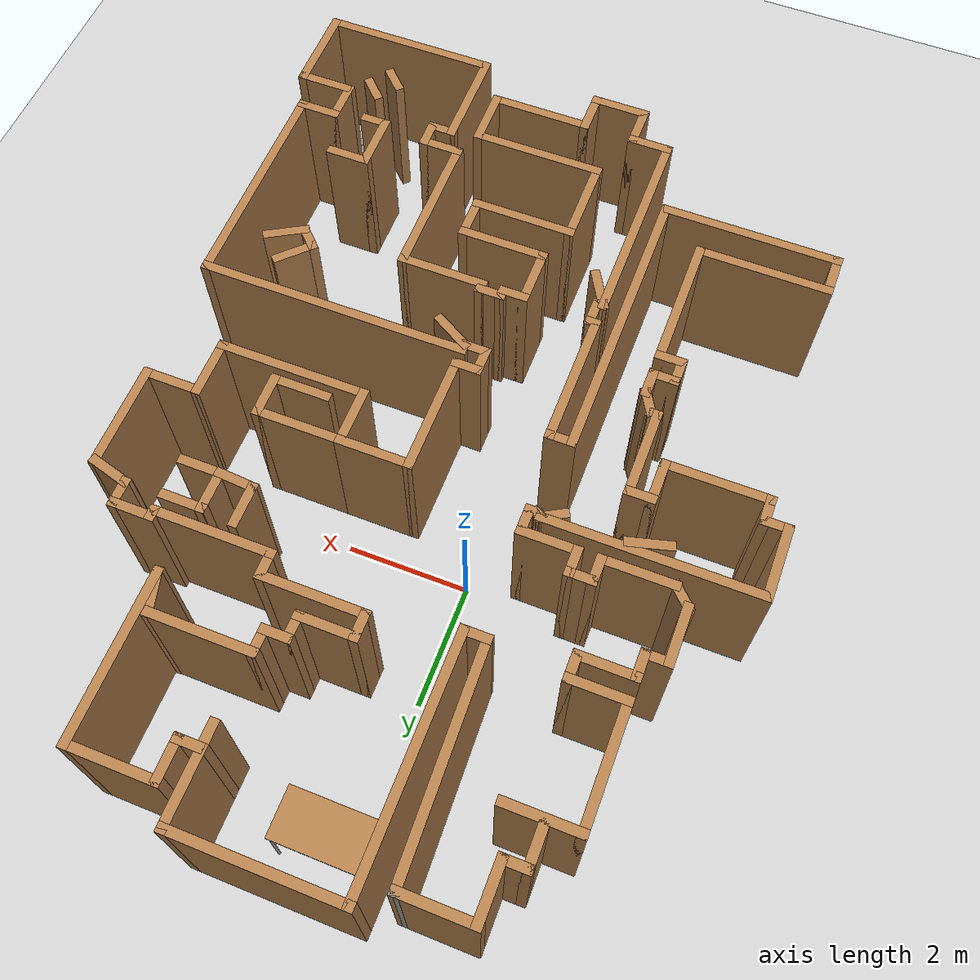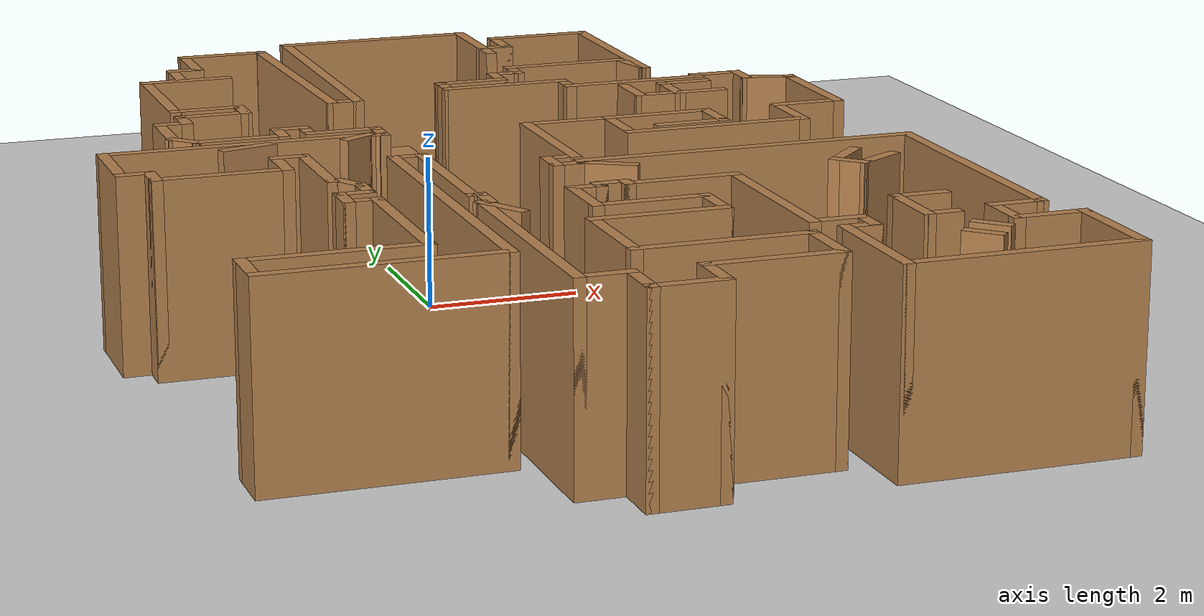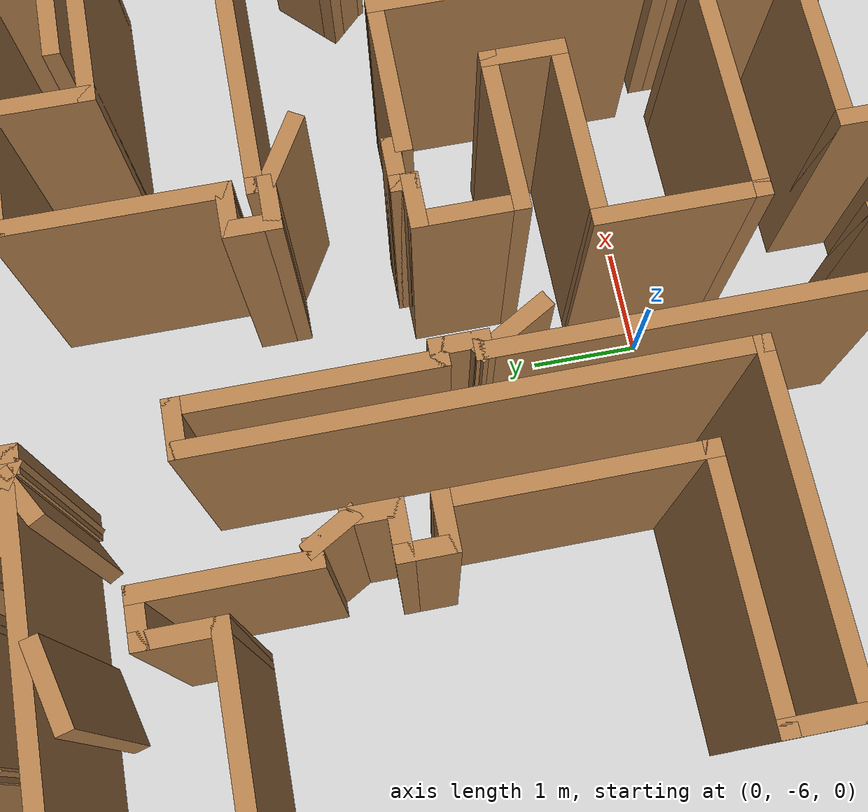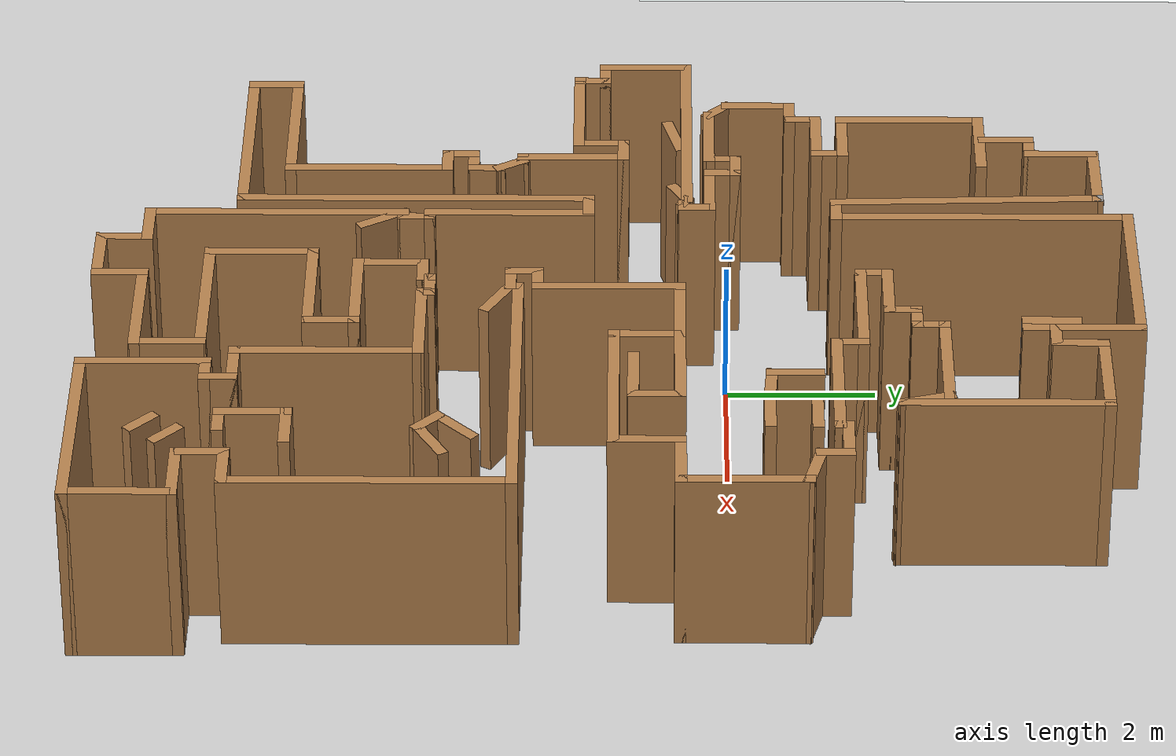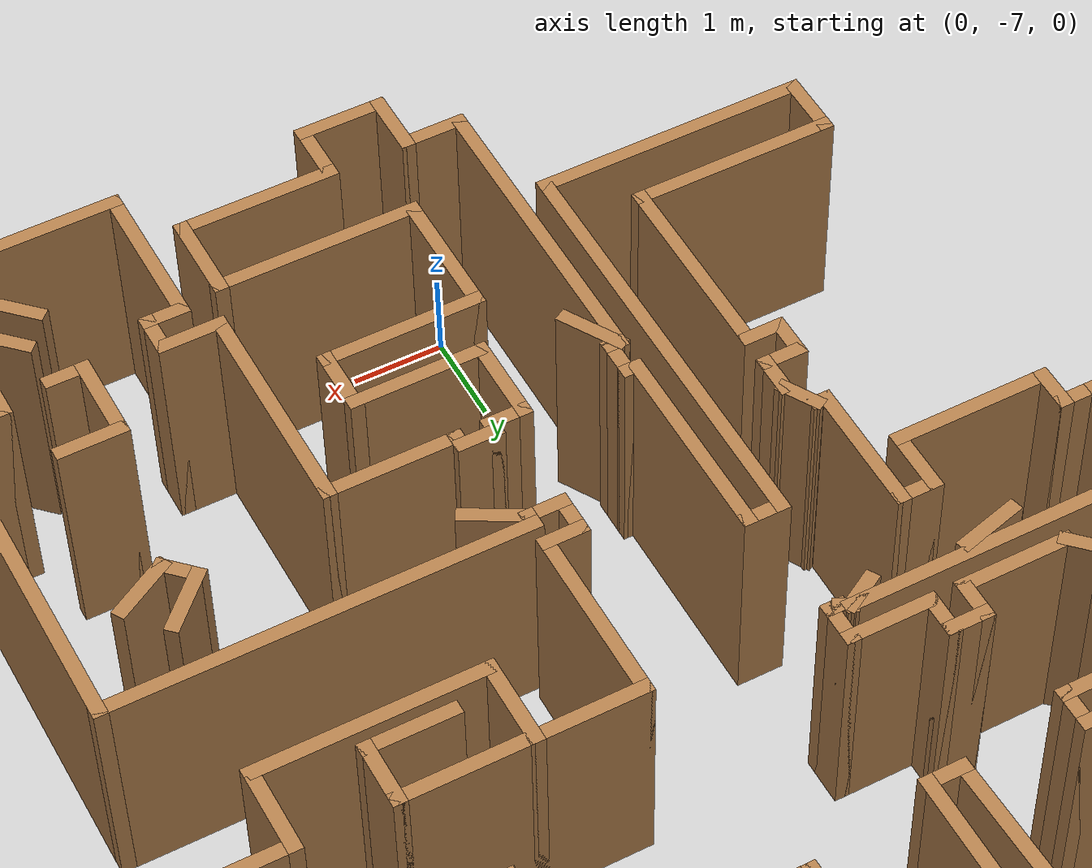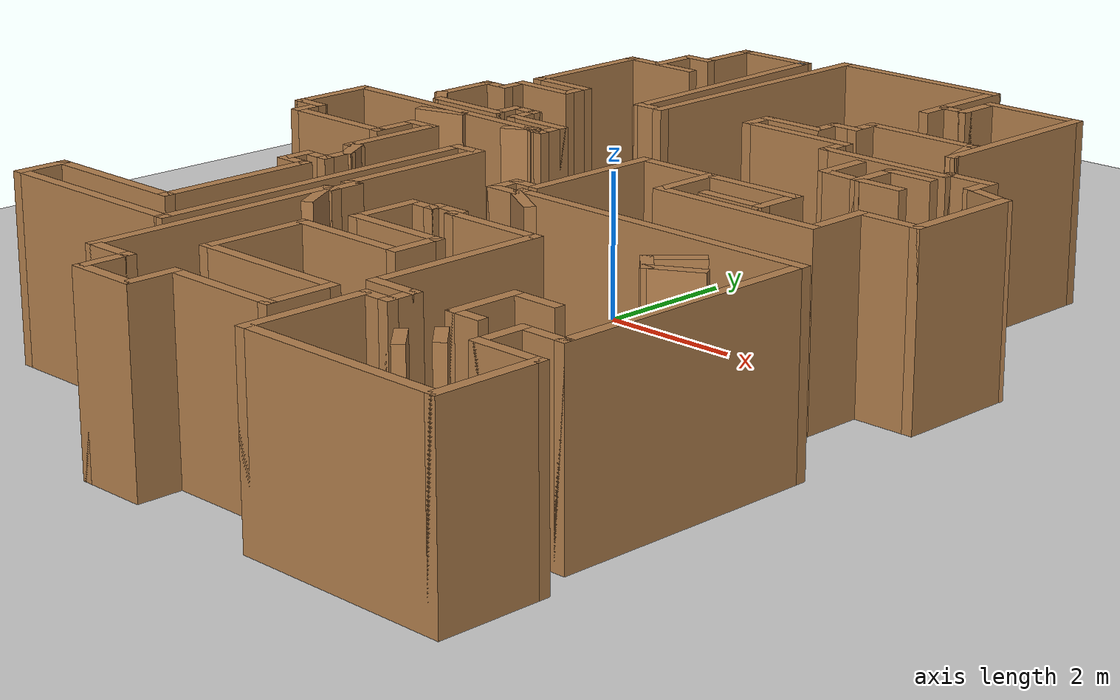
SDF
<sdf version="1.6">
 <world name="default">
  <light name="sun" type="directional">
   <pose>0 0 10 0 -0 0</pose>
   <diffuse>0.8 0.8 0.8 1</diffuse>
   <specular>0.2 0.2 0.2 1</specular>
   <attenuation>
    <range>1000</range>
    <constant>0.9</constant>
    <linear>0.01</linear>
    <quadratic>0.001</quadratic>
   </attenuation>
   <direction>-0.5 0.1 -0.9</direction>
  </light>
  <model name="ground_plane">
   <static>1</static>
   <link name="link">
    <collision name="collision">
     <geometry><plane><normal>0 0 1</normal><size>100 100</size></plane></geometry>
     <surface>
      <contact><collide_bitmask>65535</collide_bitmask></contact>
      <friction><ode><mu>100</mu><mu2>50</mu2></ode></friction>
     </surface>
    </collision>
    <visual name="visual">
     <cast_shadows>0</cast_shadows>
     <geometry><plane><normal>0 0 1</normal><size>100 100</size></plane></geometry>
     <material>
      <script><uri>file://media/materials/scripts/gazebo.material</uri><name>Gazebo/Grey</name></script>
     </material>
    </visual>
   </link>
  </model>
  <gravity>0 0 -9.8</gravity>
  <magnetic_field>6e-06 2.3e-05 -4.2e-05</magnetic_field>
  <atmosphere type="adiabatic"/>
  <physics name="default_physics" default="0" type="ode">
   <max_step_size>0.001</max_step_size>
   <real_time_factor>1</real_time_factor>
   <real_time_update_rate>1000</real_time_update_rate>
  </physics>
  <scene><ambient>0.4 0.4 0.4 1</ambient><background>0.7 0.7 0.7 1</background><shadows>1</shadows></scene>
  <audio><device>default</device></audio>
  <spherical_coordinates>
   <surface_model>EARTH_WGS84</surface_model>
   <latitude_deg>0</latitude_deg>
   <longitude_deg>0</longitude_deg>
   <elevation>0</elevation>
   <heading_deg>0</heading_deg>
  </spherical_coordinates>
  <model name="map_47">
   <pose>0.712 -1.49736 0 0 -0 0</pose>
   <link name="Wall_0">
    <collision name="Wall_0_Collision">
     <geometry><box><size>1.25 0.15 2.5</size></box></geometry>
     <pose>0 0 1.25 0 -0 0</pose>
    </collision>
    <visual name="Wall_0_Visual">
     <pose>0 0 1.25 0 -0 0</pose>
     <geometry><box><size>1.25 0.15 2.5</size></box></geometry>
     <material>
      <script><uri>file://media/materials/scripts/gazebo.material</uri><name>Gazebo/Wood</name></script>
      <ambient>1 1 1 1</ambient>
     </material>
     <meta><layer>0</layer></meta>
    </visual>
    <pose>-2.27237 6.42125 0 0 -0 3.14159</pose>
   </link>
   <link name="Wall_1">
    <collision name="Wall_1_Collision">
     <geometry><box><size>1 0.15 2.5</size></box></geometry>
     <pose>0 0 1.25 0 -0 0</pose>
    </collision>
    <visual name="Wall_1_Visual">
     <pose>0 0 1.25 0 -0 0</pose>
     <geometry><box><size>1 0.15 2.5</size></box></geometry>
     <material>
      <script><uri>file://media/materials/scripts/gazebo.material</uri><name>Gazebo/Wood</name></script>
      <ambient>1 1 1 1</ambient>
     </material>
     <meta><layer>0</layer></meta>
    </visual>
    <pose>-2.82237 5.99625 0 0 -0 -1.5708</pose>
   </link>
   <link name="Wall_10">
    <collision name="Wall_10_Collision">
     <geometry><box><size>1 0.15 2.5</size></box></geometry>
     <pose>0 0 1.25 0 -0 0</pose>
    </collision>
    <visual name="Wall_10_Visual">
     <pose>0 0 1.25 0 -0 0</pose>
     <geometry><box><size>1 0.15 2.5</size></box></geometry>
     <material>
      <script><uri>file://media/materials/scripts/gazebo.material</uri><name>Gazebo/Wood</name></script>
      <ambient>1 1 1 1</ambient>
     </material>
     <meta><layer>0</layer></meta>
    </visual>
    <pose>-3.24838 3.06273 0 0 -0 0</pose>
   </link>
   <link name="Wall_102">
    <collision name="Wall_102_Collision">
     <geometry><box><size>4.5 0.15 2.5</size></box></geometry>
     <pose>0 0 1.25 0 -0 0</pose>
    </collision>
    <visual name="Wall_102_Visual">
     <pose>0 0 1.25 0 -0 0</pose>
     <geometry><box><size>4.5 0.15 2.5</size></box></geometry>
     <material>
      <script><uri>file://media/materials/scripts/gazebo.material</uri><name>Gazebo/Wood</name></script>
      <ambient>1 1 1 1</ambient>
     </material>
     <meta><layer>0</layer></meta>
    </visual>
    <pose>2.5875 -1.23787 0 0 -0 3.14159</pose>
   </link>
   <link name="Wall_105">
    <collision name="Wall_105_Collision">
     <geometry><box><size>0.25 0.15 2.5</size></box></geometry>
     <pose>0 0 1.25 0 -0 0</pose>
    </collision>
    <visual name="Wall_105_Visual">
     <pose>0 0 1.25 0 -0 0</pose>
     <geometry><box><size>0.25 0.15 2.5</size></box></geometry>
     <material>
      <script><uri>file://media/materials/scripts/gazebo.material</uri><name>Gazebo/Wood</name></script>
      <ambient>1 1 1 1</ambient>
     </material>
     <meta><layer>0</layer></meta>
    </visual>
    <pose>0.4125 -1.28787 0 0 -0 -1.5708</pose>
   </link>
   <link name="Wall_106">
    <collision name="Wall_106_Collision">
     <geometry><box><size>0.5 0.15 2.5</size></box></geometry>
     <pose>0 0 1.25 0 -0 0</pose>
    </collision>
    <visual name="Wall_106_Visual">
     <pose>0 0 1.25 0 -0 0</pose>
     <geometry><box><size>0.5 0.15 2.5</size></box></geometry>
     <material>
      <script><uri>file://media/materials/scripts/gazebo.material</uri><name>Gazebo/Wood</name></script>
      <ambient>1 1 1 1</ambient>
     </material>
     <meta><layer>0</layer></meta>
    </visual>
    <pose>0.2375 -1.33787 0 0 -0 3.14159</pose>
   </link>
   <link name="Wall_107">
    <collision name="Wall_107_Collision">
     <geometry><box><size>0.5 0.15 2.5</size></box></geometry>
     <pose>0 0 1.25 0 -0 0</pose>
    </collision>
    <visual name="Wall_107_Visual">
     <pose>0 0 1.25 0 -0 0</pose>
     <geometry><box><size>0.5 0.15 2.5</size></box></geometry>
     <material>
      <script><uri>file://media/materials/scripts/gazebo.material</uri><name>Gazebo/Wood</name></script>
      <ambient>1 1 1 1</ambient>
     </material>
     <meta><layer>0</layer></meta>
    </visual>
    <pose>0.0625 -1.16287 0 0 -0 1.5708</pose>
   </link>
   <link name="Wall_108">
    <collision name="Wall_108_Collision">
     <geometry><box><size>0.5 0.15 2.5</size></box></geometry>
     <pose>0 0 1.25 0 -0 0</pose>
    </collision>
    <visual name="Wall_108_Visual">
     <pose>0 0 1.25 0 -0 0</pose>
     <geometry><box><size>0.5 0.15 2.5</size></box></geometry>
     <material>
      <script><uri>file://media/materials/scripts/gazebo.material</uri><name>Gazebo/Wood</name></script>
      <ambient>1 1 1 1</ambient>
     </material>
     <meta><layer>0</layer></meta>
    </visual>
    <pose>0.2375 -0.987868 0 0 -0 0</pose>
   </link>
   <link name="Wall_109">
    <collision name="Wall_109_Collision">
     <geometry><box><size>2 0.15 2.5</size></box></geometry>
     <pose>0 0 1.25 0 -0 0</pose>
    </collision>
    <visual name="Wall_109_Visual">
     <pose>0 0 1.25 0 -0 0</pose>
     <geometry><box><size>2 0.15 2.5</size></box></geometry>
     <material>
      <script><uri>file://media/materials/scripts/gazebo.material</uri><name>Gazebo/Wood</name></script>
      <ambient>1 1 1 1</ambient>
     </material>
     <meta><layer>0</layer></meta>
    </visual>
    <pose>0.4125 -0.062868 0 0 -0 1.5708</pose>
   </link>
   <link name="Wall_11">
    <collision name="Wall_11_Collision">
     <geometry><box><size>0.5 0.15 2.5</size></box></geometry>
     <pose>0 0 1.25 0 -0 0</pose>
    </collision>
    <visual name="Wall_11_Visual">
     <pose>0 0 1.25 0 -0 0</pose>
     <geometry><box><size>0.5 0.15 2.5</size></box></geometry>
     <material>
      <script><uri>file://media/materials/scripts/gazebo.material</uri><name>Gazebo/Wood</name></script>
      <ambient>1 1 1 1</ambient>
     </material>
     <meta><layer>0</layer></meta>
    </visual>
    <pose>-2.82339 2.88773 0 0 -0 -1.5708</pose>
   </link>
   <link name="Wall_110">
    <collision name="Wall_110_Collision">
     <geometry><box><size>1.25 0.15 2.5</size></box></geometry>
     <pose>0 0 1.25 0 -0 0</pose>
    </collision>
    <visual name="Wall_110_Visual">
     <pose>0 0 1.25 0 -0 0</pose>
     <geometry><box><size>1.25 0.15 2.5</size></box></geometry>
     <material>
      <script><uri>file://media/materials/scripts/gazebo.material</uri><name>Gazebo/Wood</name></script>
      <ambient>1 1 1 1</ambient>
     </material>
     <meta><layer>0</layer></meta>
    </visual>
    <pose>0.9625 0.862132 0 0 -0 0</pose>
   </link>
   <link name="Wall_111">
    <collision name="Wall_111_Collision">
     <geometry><box><size>1 0.15 2.5</size></box></geometry>
     <pose>0 0 1.25 0 -0 0</pose>
    </collision>
    <visual name="Wall_111_Visual">
     <pose>0 0 1.25 0 -0 0</pose>
     <geometry><box><size>1 0.15 2.5</size></box></geometry>
     <material>
      <script><uri>file://media/materials/scripts/gazebo.material</uri><name>Gazebo/Wood</name></script>
      <ambient>1 1 1 1</ambient>
     </material>
     <meta><layer>0</layer></meta>
    </visual>
    <pose>1.5125 0.437132 0 0 -0 -1.5708</pose>
   </link>
   <link name="Wall_112">
    <collision name="Wall_112_Collision">
     <geometry><box><size>2.5 0.15 2.5</size></box></geometry>
     <pose>0 0 1.25 0 -0 0</pose>
    </collision>
    <visual name="Wall_112_Visual">
     <pose>0 0 1.25 0 -0 0</pose>
     <geometry><box><size>2.5 0.15 2.5</size></box></geometry>
     <material>
      <script><uri>file://media/materials/scripts/gazebo.material</uri><name>Gazebo/Wood</name></script>
      <ambient>1 1 1 1</ambient>
     </material>
     <meta><layer>0</layer></meta>
    </visual>
    <pose>2.6875 0.012132 0 0 -0 0</pose>
   </link>
   <link name="Wall_113">
    <collision name="Wall_113_Collision">
     <geometry><box><size>1 0.15 2.5</size></box></geometry>
     <pose>0 0 1.25 0 -0 0</pose>
    </collision>
    <visual name="Wall_113_Visual">
     <pose>0 0 1.25 0 -0 0</pose>
     <geometry><box><size>1 0.15 2.5</size></box></geometry>
     <material>
      <script><uri>file://media/materials/scripts/gazebo.material</uri><name>Gazebo/Wood</name></script>
      <ambient>1 1 1 1</ambient>
     </material>
     <meta><layer>0</layer></meta>
    </visual>
    <pose>3.8625 0.437132 0 0 -0 1.5708</pose>
   </link>
   <link name="Wall_114">
    <collision name="Wall_114_Collision">
     <geometry><box><size>1 0.15 2.5</size></box></geometry>
     <pose>0 0 1.25 0 -0 0</pose>
    </collision>
    <visual name="Wall_114_Visual">
     <pose>0 0 1.25 0 -0 0</pose>
     <geometry><box><size>1 0.15 2.5</size></box></geometry>
     <material>
      <script><uri>file://media/materials/scripts/gazebo.material</uri><name>Gazebo/Wood</name></script>
      <ambient>1 1 1 1</ambient>
     </material>
     <meta><layer>0</layer></meta>
    </visual>
    <pose>4.2875 0.862132 0 0 -0 0</pose>
   </link>
   <link name="Wall_115">
    <collision name="Wall_115_Collision">
     <geometry><box><size>1.75 0.15 2.5</size></box></geometry>
     <pose>0 0 1.25 0 -0 0</pose>
    </collision>
    <visual name="Wall_115_Visual">
     <pose>0 0 1.25 0 -0 0</pose>
     <geometry><box><size>1.75 0.15 2.5</size></box></geometry>
     <material>
      <script><uri>file://media/materials/scripts/gazebo.material</uri><name>Gazebo/Wood</name></script>
      <ambient>1 1 1 1</ambient>
     </material>
     <meta><layer>0</layer></meta>
    </visual>
    <pose>4.7125 1.66213 0 0 -0 1.5708</pose>
   </link>
   <link name="Wall_116">
    <collision name="Wall_116_Collision">
     <geometry><box><size>0.75 0.15 2.5</size></box></geometry>
     <pose>0 0 1.25 0 -0 0</pose>
    </collision>
    <visual name="Wall_116_Visual">
     <pose>0 0 1.25 0 -0 0</pose>
     <geometry><box><size>0.75 0.15 2.5</size></box></geometry>
     <material>
      <script><uri>file://media/materials/scripts/gazebo.material</uri><name>Gazebo/Wood</name></script>
      <ambient>1 1 1 1</ambient>
     </material>
     <meta><layer>0</layer></meta>
    </visual>
    <pose>4.42272 2.53978 0 0 -0 2.87979</pose>
   </link>
   <link name="Wall_117">
    <collision name="Wall_117_Collision">
     <geometry><box><size>0.5 0.15 2.5</size></box></geometry>
     <pose>0 0 1.25 0 -0 0</pose>
    </collision>
    <visual name="Wall_117_Visual">
     <pose>0 0 1.25 0 -0 0</pose>
     <geometry><box><size>0.5 0.15 2.5</size></box></geometry>
     <material>
      <script><uri>file://media/materials/scripts/gazebo.material</uri><name>Gazebo/Wood</name></script>
      <ambient>1 1 1 1</ambient>
     </material>
     <meta><layer>0</layer></meta>
    </visual>
    <pose>4.13295 2.79242 0 0 -0 1.5708</pose>
   </link>
   <link name="Wall_118">
    <collision name="Wall_118_Collision">
     <geometry><box><size>0.75 0.15 2.5</size></box></geometry>
     <pose>0 0 1.25 0 -0 0</pose>
    </collision>
    <visual name="Wall_118_Visual">
     <pose>0 0 1.25 0 -0 0</pose>
     <geometry><box><size>0.75 0.15 2.5</size></box></geometry>
     <material>
      <script><uri>file://media/materials/scripts/gazebo.material</uri><name>Gazebo/Wood</name></script>
      <ambient>1 1 1 1</ambient>
     </material>
     <meta><layer>0</layer></meta>
    </visual>
    <pose>3.83294 2.96742 0 0 -0 3.14159</pose>
   </link>
   <link name="Wall_119">
    <collision name="Wall_119_Collision">
     <geometry><box><size>0.25 0.15 2.5</size></box></geometry>
     <pose>0 0 1.25 0 -0 0</pose>
    </collision>
    <visual name="Wall_119_Visual">
     <pose>0 0 1.25 0 -0 0</pose>
     <geometry><box><size>0.25 0.15 2.5</size></box></geometry>
     <material>
      <script><uri>file://media/materials/scripts/gazebo.material</uri><name>Gazebo/Wood</name></script>
      <ambient>1 1 1 1</ambient>
     </material>
     <meta><layer>0</layer></meta>
    </visual>
    <pose>3.53294 2.91742 0 0 -0 -1.5708</pose>
   </link>
   <link name="Wall_12">
    <collision name="Wall_12_Collision">
     <geometry><box><size>1 0.15 2.5</size></box></geometry>
     <pose>0 0 1.25 0 -0 0</pose>
    </collision>
    <visual name="Wall_12_Visual">
     <pose>0 0 1.25 0 -0 0</pose>
     <geometry><box><size>1 0.15 2.5</size></box></geometry>
     <material>
      <script><uri>file://media/materials/scripts/gazebo.material</uri><name>Gazebo/Wood</name></script>
      <ambient>1 1 1 1</ambient>
     </material>
     <meta><layer>0</layer></meta>
    </visual>
    <pose>-3.24838 2.71273 0 0 -0 3.14159</pose>
   </link>
   <link name="Wall_120">
    <collision name="Wall_120_Collision">
     <geometry><box><size>2 0.15 2.5</size></box></geometry>
     <pose>0 0 1.25 0 -0 0</pose>
    </collision>
    <visual name="Wall_120_Visual">
     <pose>0 0 1.25 0 -0 0</pose>
     <geometry><box><size>2 0.15 2.5</size></box></geometry>
     <material>
      <script><uri>file://media/materials/scripts/gazebo.material</uri><name>Gazebo/Wood</name></script>
      <ambient>1 1 1 1</ambient>
     </material>
     <meta><layer>0</layer></meta>
    </visual>
    <pose>2.60794 2.86742 0 0 -0 3.14159</pose>
   </link>
   <link name="Wall_121">
    <collision name="Wall_121_Collision">
     <geometry><box><size>0.5 0.15 2.5</size></box></geometry>
     <pose>0 0 1.25 0 -0 0</pose>
    </collision>
    <visual name="Wall_121_Visual">
     <pose>0 0 1.25 0 -0 0</pose>
     <geometry><box><size>0.5 0.15 2.5</size></box></geometry>
     <material>
      <script><uri>file://media/materials/scripts/gazebo.material</uri><name>Gazebo/Wood</name></script>
      <ambient>1 1 1 1</ambient>
     </material>
     <meta><layer>0</layer></meta>
    </visual>
    <pose>1.68294 3.04242 0 0 -0 1.5708</pose>
   </link>
   <link name="Wall_122">
    <collision name="Wall_122_Collision">
     <geometry><box><size>1.75 0.15 2.5</size></box></geometry>
     <pose>0 0 1.25 0 -0 0</pose>
    </collision>
    <visual name="Wall_122_Visual">
     <pose>0 0 1.25 0 -0 0</pose>
     <geometry><box><size>1.75 0.15 2.5</size></box></geometry>
     <material>
      <script><uri>file://media/materials/scripts/gazebo.material</uri><name>Gazebo/Wood</name></script>
      <ambient>1 1 1 1</ambient>
     </material>
     <meta><layer>0</layer></meta>
    </visual>
    <pose>0.882944 3.21742 0 0 -0 3.14159</pose>
   </link>
   <link name="Wall_123">
    <collision name="Wall_123_Collision">
     <geometry><box><size>0.5 0.15 2.5</size></box></geometry>
     <pose>0 0 1.25 0 -0 0</pose>
    </collision>
    <visual name="Wall_123_Visual">
     <pose>0 0 1.25 0 -0 0</pose>
     <geometry><box><size>0.5 0.15 2.5</size></box></geometry>
     <material>
      <script><uri>file://media/materials/scripts/gazebo.material</uri><name>Gazebo/Wood</name></script>
      <ambient>1 1 1 1</ambient>
     </material>
     <meta><layer>0</layer></meta>
    </visual>
    <pose>0.082945 3.39242 0 0 -0 1.5708</pose>
   </link>
   <link name="Wall_126">
    <collision name="Wall_126_Collision">
     <geometry><box><size>1 0.15 2.5</size></box></geometry>
     <pose>0 0 1.25 0 -0 0</pose>
    </collision>
    <visual name="Wall_126_Visual">
     <pose>0 0 1.25 0 -0 0</pose>
     <geometry><box><size>1 0.15 2.5</size></box></geometry>
     <material>
      <script><uri>file://media/materials/scripts/gazebo.material</uri><name>Gazebo/Wood</name></script>
      <ambient>1 1 1 1</ambient>
     </material>
     <meta><layer>0</layer></meta>
    </visual>
    <pose>0.507945 3.56742 0 0 -0 0</pose>
   </link>
   <link name="Wall_127">
    <collision name="Wall_127_Collision">
     <geometry><box><size>0.5 0.15 2.5</size></box></geometry>
     <pose>0 0 1.25 0 -0 0</pose>
    </collision>
    <visual name="Wall_127_Visual">
     <pose>0 0 1.25 0 -0 0</pose>
     <geometry><box><size>0.5 0.15 2.5</size></box></geometry>
     <material>
      <script><uri>file://media/materials/scripts/gazebo.material</uri><name>Gazebo/Wood</name></script>
      <ambient>1 1 1 1</ambient>
     </material>
     <meta><layer>0</layer></meta>
    </visual>
    <pose>0.932945 3.74242 0 0 -0 1.5708</pose>
   </link>
   <link name="Wall_128">
    <collision name="Wall_128_Collision">
     <geometry><box><size>0.5 0.15 2.5</size></box></geometry>
     <pose>0 0 1.25 0 -0 0</pose>
    </collision>
    <visual name="Wall_128_Visual">
     <pose>0 0 1.25 0 -0 0</pose>
     <geometry><box><size>0.5 0.15 2.5</size></box></geometry>
     <material>
      <script><uri>file://media/materials/scripts/gazebo.material</uri><name>Gazebo/Wood</name></script>
      <ambient>1 1 1 1</ambient>
     </material>
     <meta><layer>0</layer></meta>
    </visual>
    <pose>1.10794 3.91742 0 0 -0 0</pose>
   </link>
   <link name="Wall_129">
    <collision name="Wall_129_Collision">
     <geometry><box><size>0.5 0.15 2.5</size></box></geometry>
     <pose>0 0 1.25 0 -0 0</pose>
    </collision>
    <visual name="Wall_129_Visual">
     <pose>0 0 1.25 0 -0 0</pose>
     <geometry><box><size>0.5 0.15 2.5</size></box></geometry>
     <material>
      <script><uri>file://media/materials/scripts/gazebo.material</uri><name>Gazebo/Wood</name></script>
      <ambient>1 1 1 1</ambient>
     </material>
     <meta><layer>0</layer></meta>
    </visual>
    <pose>1.28295 4.09242 0 0 -0 1.5708</pose>
   </link>
   <link name="Wall_13">
    <collision name="Wall_13_Collision">
     <geometry><box><size>0.5 0.15 2.5</size></box></geometry>
     <pose>0 0 1.25 0 -0 0</pose>
    </collision>
    <visual name="Wall_13_Visual">
     <pose>0 0 1.25 0 -0 0</pose>
     <geometry><box><size>0.5 0.15 2.5</size></box></geometry>
     <material>
      <script><uri>file://media/materials/scripts/gazebo.material</uri><name>Gazebo/Wood</name></script>
      <ambient>1 1 1 1</ambient>
     </material>
     <meta><layer>0</layer></meta>
    </visual>
    <pose>-3.67339 2.53773 0 0 -0 -1.5708</pose>
   </link>
   <link name="Wall_130">
    <collision name="Wall_130_Collision">
     <geometry><box><size>1.75 0.15 2.5</size></box></geometry>
     <pose>0 0 1.25 0 -0 0</pose>
    </collision>
    <visual name="Wall_130_Visual">
     <pose>0 0 1.25 0 -0 0</pose>
     <geometry><box><size>1.75 0.15 2.5</size></box></geometry>
     <material>
      <script><uri>file://media/materials/scripts/gazebo.material</uri><name>Gazebo/Wood</name></script>
      <ambient>1 1 1 1</ambient>
     </material>
     <meta><layer>0</layer></meta>
    </visual>
    <pose>2.08294 4.26742 0 0 -0 0</pose>
   </link>
   <link name="Wall_131">
    <collision name="Wall_131_Collision">
     <geometry><box><size>0.75 0.15 2.5</size></box></geometry>
     <pose>0 0 1.25 0 -0 0</pose>
    </collision>
    <visual name="Wall_131_Visual">
     <pose>0 0 1.25 0 -0 0</pose>
     <geometry><box><size>0.75 0.15 2.5</size></box></geometry>
     <material>
      <script><uri>file://media/materials/scripts/gazebo.material</uri><name>Gazebo/Wood</name></script>
      <ambient>1 1 1 1</ambient>
     </material>
     <meta><layer>0</layer></meta>
    </visual>
    <pose>2.96059 3.97765 0 0 -0 -1.309</pose>
   </link>
   <link name="Wall_132">
    <collision name="Wall_132_Collision">
     <geometry><box><size>2.75 0.15 2.5</size></box></geometry>
     <pose>0 0 1.25 0 -0 0</pose>
    </collision>
    <visual name="Wall_132_Visual">
     <pose>0 0 1.25 0 -0 0</pose>
     <geometry><box><size>2.75 0.15 2.5</size></box></geometry>
     <material>
      <script><uri>file://media/materials/scripts/gazebo.material</uri><name>Gazebo/Wood</name></script>
      <ambient>1 1 1 1</ambient>
     </material>
     <meta><layer>0</layer></meta>
    </visual>
    <pose>3.03824 4.98787 0 0 -0 1.5708</pose>
   </link>
   <link name="Wall_133">
    <collision name="Wall_133_Collision">
     <geometry><box><size>1.5 0.15 2.5</size></box></geometry>
     <pose>0 0 1.25 0 -0 0</pose>
    </collision>
    <visual name="Wall_133_Visual">
     <pose>0 0 1.25 0 -0 0</pose>
     <geometry><box><size>1.5 0.15 2.5</size></box></geometry>
     <material>
      <script><uri>file://media/materials/scripts/gazebo.material</uri><name>Gazebo/Wood</name></script>
      <ambient>1 1 1 1</ambient>
     </material>
     <meta><layer>0</layer></meta>
    </visual>
    <pose>2.36324 6.28787 0 0 -0 3.14159</pose>
   </link>
   <link name="Wall_134">
    <collision name="Wall_134_Collision">
     <geometry><box><size>0.75 0.15 2.5</size></box></geometry>
     <pose>0 0 1.25 0 -0 0</pose>
    </collision>
    <visual name="Wall_134_Visual">
     <pose>0 0 1.25 0 -0 0</pose>
     <geometry><box><size>0.75 0.15 2.5</size></box></geometry>
     <material>
      <script><uri>file://media/materials/scripts/gazebo.material</uri><name>Gazebo/Wood</name></script>
      <ambient>1 1 1 1</ambient>
     </material>
     <meta><layer>0</layer></meta>
    </visual>
    <pose>1.68824 5.98787 0 0 -0 -1.5708</pose>
   </link>
   <link name="Wall_135">
    <collision name="Wall_135_Collision">
     <geometry><box><size>0.5 0.15 2.5</size></box></geometry>
     <pose>0 0 1.25 0 -0 0</pose>
    </collision>
    <visual name="Wall_135_Visual">
     <pose>0 0 1.25 0 -0 0</pose>
     <geometry><box><size>0.5 0.15 2.5</size></box></geometry>
     <material>
      <script><uri>file://media/materials/scripts/gazebo.material</uri><name>Gazebo/Wood</name></script>
      <ambient>1 1 1 1</ambient>
     </material>
     <meta><layer>0</layer></meta>
    </visual>
    <pose>1.51324 5.68787 0 0 -0 3.14159</pose>
   </link>
   <link name="Wall_136">
    <collision name="Wall_136_Collision">
     <geometry><box><size>1.25 0.15 2.5</size></box></geometry>
     <pose>0 0 1.25 0 -0 0</pose>
    </collision>
    <visual name="Wall_136_Visual">
     <pose>0 0 1.25 0 -0 0</pose>
     <geometry><box><size>1.25 0.15 2.5</size></box></geometry>
     <material>
      <script><uri>file://media/materials/scripts/gazebo.material</uri><name>Gazebo/Wood</name></script>
      <ambient>1 1 1 1</ambient>
     </material>
     <meta><layer>0</layer></meta>
    </visual>
    <pose>1.33824 6.23787 0 0 -0 1.5708</pose>
   </link>
   <link name="Wall_137">
    <collision name="Wall_137_Collision">
     <geometry><box><size>2.75 0.15 2.5</size></box></geometry>
     <pose>0 0 1.25 0 -0 0</pose>
    </collision>
    <visual name="Wall_137_Visual">
     <pose>0 0 1.25 0 -0 0</pose>
     <geometry><box><size>2.75 0.15 2.5</size></box></geometry>
     <material>
      <script><uri>file://media/materials/scripts/gazebo.material</uri><name>Gazebo/Wood</name></script>
      <ambient>1 1 1 1</ambient>
     </material>
     <meta><layer>0</layer></meta>
    </visual>
    <pose>0.038236 6.78787 0 0 -0 3.14159</pose>
   </link>
   <link name="Wall_138">
    <collision name="Wall_138_Collision">
     <geometry><box><size>4 0.15 2.5</size></box></geometry>
     <pose>0 0 1.25 0 -0 0</pose>
    </collision>
    <visual name="Wall_138_Visual">
     <pose>0 0 1.25 0 -0 0</pose>
     <geometry><box><size>4 0.15 2.5</size></box></geometry>
     <material>
      <script><uri>file://media/materials/scripts/gazebo.material</uri><name>Gazebo/Wood</name></script>
      <ambient>1 1 1 1</ambient>
     </material>
     <meta><layer>0</layer></meta>
    </visual>
    <pose>-1.26176 4.86287 0 0 -0 -1.5708</pose>
   </link>
   <link name="Wall_139">
    <collision name="Wall_139_Collision">
     <geometry><box><size>0.5 0.15 2.5</size></box></geometry>
     <pose>0 0 1.25 0 -0 0</pose>
    </collision>
    <visual name="Wall_139_Visual">
     <pose>0 0 1.25 0 -0 0</pose>
     <geometry><box><size>0.5 0.15 2.5</size></box></geometry>
     <material>
      <script><uri>file://media/materials/scripts/gazebo.material</uri><name>Gazebo/Wood</name></script>
      <ambient>1 1 1 1</ambient>
     </material>
     <meta><layer>0</layer></meta>
    </visual>
    <pose>-1.43676 2.93787 0 0 -0 3.14159</pose>
   </link>
   <link name="Wall_141">
    <collision name="Wall_141_Collision">
     <geometry><box><size>0.15 0.15 2.5</size></box></geometry>
     <pose>0 0 1.25 0 -0 0</pose>
    </collision>
    <visual name="Wall_141_Visual">
     <pose>0 0 1.25 0 -0 0</pose>
     <geometry><box><size>0.15 0.15 2.5</size></box></geometry>
     <material>
      <script><uri>file://media/materials/scripts/gazebo.material</uri><name>Gazebo/Grey</name></script>
      <ambient>1 1 1 1</ambient>
     </material>
     <meta><layer>0</layer></meta>
    </visual>
    <pose>-1.72237 6.42125 0 0 -0 0</pose>
   </link>
   <link name="Wall_144">
    <collision name="Wall_144_Collision">
     <geometry><box><size>3.63513 0.15 2.5</size></box></geometry>
     <pose>0 0 1.25 0 -0 0</pose>
    </collision>
    <visual name="Wall_144_Visual">
     <pose>0 0 1.25 0 -0 0</pose>
     <geometry><box><size>3.63513 0.15 2.5</size></box></geometry>
     <material>
      <script><uri>file://media/materials/scripts/gazebo.material</uri><name>Gazebo/Wood</name></script>
      <ambient>1 1 1 1</ambient>
     </material>
     <meta><layer>0</layer></meta>
    </visual>
    <pose>-1.66707 4.67956 0 0 -0 1.60254</pose>
   </link>
   <link name="Wall_146">
    <collision name="Wall_146_Collision">
     <geometry><box><size>0.5 0.15 2.5</size></box></geometry>
     <pose>0 0 1.25 0 -0 0</pose>
    </collision>
    <visual name="Wall_146_Visual">
     <pose>0 0 1.25 0 -0 0</pose>
     <geometry><box><size>0.5 0.15 2.5</size></box></geometry>
     <material>
      <script><uri>file://media/materials/scripts/gazebo.material</uri><name>Gazebo/Wood</name></script>
      <ambient>1 1 1 1</ambient>
     </material>
     <meta><layer>0</layer></meta>
    </visual>
    <pose>1.33824 5.51287 0 0 -0 -1.5708</pose>
   </link>
   <link name="Wall_148">
    <collision name="Wall_148_Collision">
     <geometry><box><size>0.75 0.15 2.5</size></box></geometry>
     <pose>0 0 1.25 0 -0 0</pose>
    </collision>
    <visual name="Wall_148_Visual">
     <pose>0 0 1.25 0 -0 0</pose>
     <geometry><box><size>0.75 0.15 2.5</size></box></geometry>
     <material>
      <script><uri>file://media/materials/scripts/gazebo.material</uri><name>Gazebo/Wood</name></script>
      <ambient>1 1 1 1</ambient>
     </material>
     <meta><layer>0</layer></meta>
    </visual>
    <pose>3.21399 2.5924 0 0 -0 3.14159</pose>
   </link>
   <link name="Wall_149">
    <collision name="Wall_149_Collision">
     <geometry><box><size>0.75 0.15 2.5</size></box></geometry>
     <pose>0 0 1.25 0 -0 0</pose>
    </collision>
    <visual name="Wall_149_Visual">
     <pose>0 0 1.25 0 -0 0</pose>
     <geometry><box><size>0.75 0.15 2.5</size></box></geometry>
     <material>
      <script><uri>file://media/materials/scripts/gazebo.material</uri><name>Gazebo/Wood</name></script>
      <ambient>1 1 1 1</ambient>
     </material>
     <meta><layer>0</layer></meta>
    </visual>
    <pose>2.91399 2.2924 0 0 -0 -1.5708</pose>
   </link>
   <link name="Wall_150">
    <collision name="Wall_150_Collision">
     <geometry><box><size>0.75 0.15 2.5</size></box></geometry>
     <pose>0 0 1.25 0 -0 0</pose>
    </collision>
    <visual name="Wall_150_Visual">
     <pose>0 0 1.25 0 -0 0</pose>
     <geometry><box><size>0.75 0.15 2.5</size></box></geometry>
     <material>
      <script><uri>file://media/materials/scripts/gazebo.material</uri><name>Gazebo/Wood</name></script>
      <ambient>1 1 1 1</ambient>
     </material>
     <meta><layer>0</layer></meta>
    </visual>
    <pose>3.21399 1.9924 0 0 -0 0</pose>
   </link>
   <link name="Wall_152">
    <collision name="Wall_152_Collision">
     <geometry><box><size>0.75 0.15 2.5</size></box></geometry>
     <pose>0 0 1.25 0 -0 0</pose>
    </collision>
    <visual name="Wall_152_Visual">
     <pose>0 0 1.25 0 -0 0</pose>
     <geometry><box><size>0.75 0.15 2.5</size></box></geometry>
     <material>
      <script><uri>file://media/materials/scripts/gazebo.material</uri><name>Gazebo/Wood</name></script>
      <ambient>1 1 1 1</ambient>
     </material>
     <meta><layer>0</layer></meta>
    </visual>
    <pose>2.37714 2.32738 0 0 -0 -1.5708</pose>
   </link>
   <link name="Wall_153">
    <collision name="Wall_153_Collision">
     <geometry><box><size>0.687992 0.15 2.5</size></box></geometry>
     <pose>0 0 1.25 0 -0 0</pose>
    </collision>
    <visual name="Wall_153_Visual">
     <pose>0 0 1.25 0 -0 0</pose>
     <geometry><box><size>0.687992 0.15 2.5</size></box></geometry>
     <material>
      <script><uri>file://media/materials/scripts/gazebo.material</uri><name>Gazebo/Wood</name></script>
      <ambient>1 1 1 1</ambient>
     </material>
     <meta><layer>0</layer></meta>
    </visual>
    <pose>2.64557 2.00989 0 0 -0 -0.065066</pose>
   </link>
   <link name="Wall_156">
    <collision name="Wall_156_Collision">
     <geometry><box><size>1.5 0.15 2.5</size></box></geometry>
     <pose>0 0 1.25 0 -0 0</pose>
    </collision>
    <visual name="Wall_156_Visual">
     <pose>0 0 1.25 0 -0 0</pose>
     <geometry><box><size>1.5 0.15 2.5</size></box></geometry>
     <material>
      <script><uri>file://media/materials/scripts/gazebo.material</uri><name>Gazebo/Wood</name></script>
      <ambient>1 1 1 1</ambient>
     </material>
     <meta><layer>0</layer></meta>
    </visual>
    <pose>2.1875 0.862132 0 0 -0 0</pose>
   </link>
   <link name="Wall_157">
    <collision name="Wall_157_Collision">
     <geometry><box><size>0.75 0.15 2.5</size></box></geometry>
     <pose>0 0 1.25 0 -0 0</pose>
    </collision>
    <visual name="Wall_157_Visual">
     <pose>0 0 1.25 0 -0 0</pose>
     <geometry><box><size>0.75 0.15 2.5</size></box></geometry>
     <material>
      <script><uri>file://media/materials/scripts/gazebo.material</uri><name>Gazebo/Wood</name></script>
      <ambient>1 1 1 1</ambient>
     </material>
     <meta><layer>0</layer></meta>
    </visual>
    <pose>2.8625 0.562132 0 0 -0 -1.5708</pose>
   </link>
   <link name="Wall_158">
    <collision name="Wall_158_Collision">
     <geometry><box><size>1 0.15 2.5</size></box></geometry>
     <pose>0 0 1.25 0 -0 0</pose>
    </collision>
    <visual name="Wall_158_Visual">
     <pose>0 0 1.25 0 -0 0</pose>
     <geometry><box><size>1 0.15 2.5</size></box></geometry>
     <material>
      <script><uri>file://media/materials/scripts/gazebo.material</uri><name>Gazebo/Wood</name></script>
      <ambient>1 1 1 1</ambient>
     </material>
     <meta><layer>0</layer></meta>
    </visual>
    <pose>2.4375 0.262132 0 0 -0 3.14159</pose>
   </link>
   <link name="Wall_16">
    <collision name="Wall_16_Collision">
     <geometry><box><size>0.5 0.15 2.5</size></box></geometry>
     <pose>0 0 1.25 0 -0 0</pose>
    </collision>
    <visual name="Wall_16_Visual">
     <pose>0 0 1.25 0 -0 0</pose>
     <geometry><box><size>0.5 0.15 2.5</size></box></geometry>
     <material>
      <script><uri>file://media/materials/scripts/gazebo.material</uri><name>Gazebo/Wood</name></script>
      <ambient>1 1 1 1</ambient>
     </material>
     <meta><layer>0</layer></meta>
    </visual>
    <pose>-3.84838 2.36273 0 0 -0 3.14159</pose>
   </link>
   <link name="Wall_164">
    <collision name="Wall_164_Collision">
     <geometry><box><size>0.5 0.15 2.5</size></box></geometry>
     <pose>0 0 1.25 0 -0 0</pose>
    </collision>
    <visual name="Wall_164_Visual">
     <pose>0 0 1.25 0 -0 0</pose>
     <geometry><box><size>0.5 0.15 2.5</size></box></geometry>
     <material>
      <script><uri>file://media/materials/scripts/gazebo.material</uri><name>Gazebo/Wood</name></script>
      <ambient>1 1 1 1</ambient>
     </material>
     <meta><layer>0</layer></meta>
    </visual>
    <pose>-1.81405 0.877741 0 0 -0 -2.61799</pose>
   </link>
   <link name="Wall_166">
    <collision name="Wall_166_Collision">
     <geometry><box><size>0.75 0.15 2.5</size></box></geometry>
     <pose>0 0 1.25 0 -0 0</pose>
    </collision>
    <visual name="Wall_166_Visual">
     <pose>0 0 1.25 0 -0 0</pose>
     <geometry><box><size>0.75 0.15 2.5</size></box></geometry>
     <material>
      <script><uri>file://media/materials/scripts/gazebo.material</uri><name>Gazebo/Wood</name></script>
      <ambient>1 1 1 1</ambient>
     </material>
     <meta><layer>0</layer></meta>
    </visual>
    <pose>-3.24472 0.798606 0 0 -0 0.261799</pose>
   </link>
   <link name="Wall_169">
    <collision name="Wall_169_Collision">
     <geometry><box><size>0.75 0.15 2.5</size></box></geometry>
     <pose>0 0 1.25 0 -0 0</pose>
    </collision>
    <visual name="Wall_169_Visual">
     <pose>0 0 1.25 0 -0 0</pose>
     <geometry><box><size>0.75 0.15 2.5</size></box></geometry>
     <material>
      <script><uri>file://media/materials/scripts/gazebo.material</uri><name>Gazebo/Wood</name></script>
      <ambient>1 1 1 1</ambient>
     </material>
     <meta><layer>0</layer></meta>
    </visual>
    <pose>0.672308 -1.48787 0 0 -0 -0.523599</pose>
   </link>
   <link name="Wall_17">
    <collision name="Wall_17_Collision">
     <geometry><box><size>1 0.15 2.5</size></box></geometry>
     <pose>0 0 1.25 0 -0 0</pose>
    </collision>
    <visual name="Wall_17_Visual">
     <pose>0 0 1.25 0 -0 0</pose>
     <geometry><box><size>1 0.15 2.5</size></box></geometry>
     <material>
      <script><uri>file://media/materials/scripts/gazebo.material</uri><name>Gazebo/Wood</name></script>
      <ambient>1 1 1 1</ambient>
     </material>
     <meta><layer>0</layer></meta>
    </visual>
    <pose>-4.02339 1.93773 0 0 -0 -1.5708</pose>
   </link>
   <link name="Wall_171">
    <collision name="Wall_171_Collision">
     <geometry><box><size>0.75 0.15 2.5</size></box></geometry>
     <pose>0 0 1.25 0 -0 0</pose>
    </collision>
    <visual name="Wall_171_Visual">
     <pose>0 0 1.25 0 -0 0</pose>
     <geometry><box><size>0.75 0.15 2.5</size></box></geometry>
     <material>
      <script><uri>file://media/materials/scripts/gazebo.material</uri><name>Gazebo/Wood</name></script>
      <ambient>1 1 1 1</ambient>
     </material>
     <meta><layer>0</layer></meta>
    </visual>
    <pose>3.57602 -1.97786 0 0 -0 -2.35619</pose>
   </link>
   <link name="Wall_172">
    <collision name="Wall_172_Collision">
     <geometry><box><size>0.5 0.15 2.5</size></box></geometry>
     <pose>0 0 1.25 0 -0 0</pose>
    </collision>
    <visual name="Wall_172_Visual">
     <pose>0 0 1.25 0 -0 0</pose>
     <geometry><box><size>0.5 0.15 2.5</size></box></geometry>
     <material>
      <script><uri>file://media/materials/scripts/gazebo.material</uri><name>Gazebo/Wood</name></script>
      <ambient>1 1 1 1</ambient>
     </material>
     <meta><layer>0</layer></meta>
    </visual>
    <pose>3.48763 -2.31373 0 0 -0 -0.785398</pose>
   </link>
   <link name="Wall_173">
    <collision name="Wall_173_Collision">
     <geometry><box><size>0.75 0.15 2.5</size></box></geometry>
     <pose>0 0 1.25 0 -0 0</pose>
    </collision>
    <visual name="Wall_173_Visual">
     <pose>0 0 1.25 0 -0 0</pose>
     <geometry><box><size>0.75 0.15 2.5</size></box></geometry>
     <material>
      <script><uri>file://media/materials/scripts/gazebo.material</uri><name>Gazebo/Wood</name></script>
      <ambient>1 1 1 1</ambient>
     </material>
     <meta><layer>0</layer></meta>
    </visual>
    <pose>3.87118 -2.28748 0 0 -0 0.523599</pose>
   </link>
   <link name="Wall_175">
    <collision name="Wall_175_Collision">
     <geometry><box><size>0.75 0.15 2.5</size></box></geometry>
     <pose>0 0 1.25 0 -0 0</pose>
    </collision>
    <visual name="Wall_175_Visual">
     <pose>0 0 1.25 0 -0 0</pose>
     <geometry><box><size>0.75 0.15 2.5</size></box></geometry>
     <material>
      <script><uri>file://media/materials/scripts/gazebo.material</uri><name>Gazebo/Wood</name></script>
      <ambient>1 1 1 1</ambient>
     </material>
     <meta><layer>0</layer></meta>
    </visual>
    <pose>3.58067 -4.10192 0 0 -0 3.14159</pose>
   </link>
   <link name="Wall_176">
    <collision name="Wall_176_Collision">
     <geometry><box><size>1 0.15 2.5</size></box></geometry>
     <pose>0 0 1.25 0 -0 0</pose>
    </collision>
    <visual name="Wall_176_Visual">
     <pose>0 0 1.25 0 -0 0</pose>
     <geometry><box><size>1 0.15 2.5</size></box></geometry>
     <material>
      <script><uri>file://media/materials/scripts/gazebo.material</uri><name>Gazebo/Wood</name></script>
      <ambient>1 1 1 1</ambient>
     </material>
     <meta><layer>0</layer></meta>
    </visual>
    <pose>3.28067 -4.52692 0 0 -0 -1.5708</pose>
   </link>
   <link name="Wall_179">
    <collision name="Wall_179_Collision">
     <geometry><box><size>0.5 0.15 2.5</size></box></geometry>
     <pose>0 0 1.25 0 -0 0</pose>
    </collision>
    <visual name="Wall_179_Visual">
     <pose>0 0 1.25 0 -0 0</pose>
     <geometry><box><size>0.5 0.15 2.5</size></box></geometry>
     <material>
      <script><uri>file://media/materials/scripts/gazebo.material</uri><name>Gazebo/Wood</name></script>
      <ambient>1 1 1 1</ambient>
     </material>
     <meta><layer>0</layer></meta>
    </visual>
    <pose>3.45567 -4.95192 0 0 -0 0</pose>
   </link>
   <link name="Wall_18">
    <collision name="Wall_18_Collision">
     <geometry><box><size>0.5 0.15 2.5</size></box></geometry>
     <pose>0 0 1.25 0 -0 0</pose>
    </collision>
    <visual name="Wall_18_Visual">
     <pose>0 0 1.25 0 -0 0</pose>
     <geometry><box><size>0.5 0.15 2.5</size></box></geometry>
     <material>
      <script><uri>file://media/materials/scripts/gazebo.material</uri><name>Gazebo/Wood</name></script>
      <ambient>1 1 1 1</ambient>
     </material>
     <meta><layer>0</layer></meta>
    </visual>
    <pose>-3.89964 1.38898 0 0 -0 -0.785398</pose>
   </link>
   <link name="Wall_181">
    <collision name="Wall_181_Collision">
     <geometry><box><size>0.5 0.15 2.5</size></box></geometry>
     <pose>0 0 1.25 0 -0 0</pose>
    </collision>
    <visual name="Wall_181_Visual">
     <pose>0 0 1.25 0 -0 0</pose>
     <geometry><box><size>0.5 0.15 2.5</size></box></geometry>
     <material>
      <script><uri>file://media/materials/scripts/gazebo.material</uri><name>Gazebo/Wood</name></script>
      <ambient>1 1 1 1</ambient>
     </material>
     <meta><layer>0</layer></meta>
    </visual>
    <pose>3.77311 -5.59037 0 0 -0 -0.785398</pose>
   </link>
   <link name="Wall_183">
    <collision name="Wall_183_Collision">
     <geometry><box><size>0.5 0.15 2.5</size></box></geometry>
     <pose>0 0 1.25 0 -0 0</pose>
    </collision>
    <visual name="Wall_183_Visual">
     <pose>0 0 1.25 0 -0 0</pose>
     <geometry><box><size>0.5 0.15 2.5</size></box></geometry>
     <material>
      <script><uri>file://media/materials/scripts/gazebo.material</uri><name>Gazebo/Wood</name></script>
      <ambient>1 1 1 1</ambient>
     </material>
     <meta><layer>0</layer></meta>
    </visual>
    <pose>3.51867 -5.9142 0 0 -0 -0.785398</pose>
   </link>
   <link name="Wall_185">
    <collision name="Wall_185_Collision">
     <geometry><box><size>0.75 0.15 2.5</size></box></geometry>
     <pose>0 0 1.25 0 -0 0</pose>
    </collision>
    <visual name="Wall_185_Visual">
     <pose>0 0 1.25 0 -0 0</pose>
     <geometry><box><size>0.75 0.15 2.5</size></box></geometry>
     <material>
      <script><uri>file://media/materials/scripts/gazebo.material</uri><name>Gazebo/Wood</name></script>
      <ambient>1 1 1 1</ambient>
     </material>
     <meta><layer>0</layer></meta>
    </visual>
    <pose>-1.1875 -3.04768 0 0 -0 -1.0472</pose>
   </link>
   <link name="Wall_19">
    <collision name="Wall_19_Collision">
     <geometry><box><size>1.25 0.15 2.5</size></box></geometry>
     <pose>0 0 1.25 0 -0 0</pose>
    </collision>
    <visual name="Wall_19_Visual">
     <pose>0 0 1.25 0 -0 0</pose>
     <geometry><box><size>1.25 0.15 2.5</size></box></geometry>
     <material>
      <script><uri>file://media/materials/scripts/gazebo.material</uri><name>Gazebo/Wood</name></script>
      <ambient>1 1 1 1</ambient>
     </material>
     <meta><layer>0</layer></meta>
    </visual>
    <pose>-3.2259 1.26524 0 0 -0 0</pose>
   </link>
   <link name="Wall_2">
    <collision name="Wall_2_Collision">
     <geometry><box><size>0.5 0.15 2.5</size></box></geometry>
     <pose>0 0 1.25 0 -0 0</pose>
    </collision>
    <visual name="Wall_2_Visual">
     <pose>0 0 1.25 0 -0 0</pose>
     <geometry><box><size>0.5 0.15 2.5</size></box></geometry>
     <material>
      <script><uri>file://media/materials/scripts/gazebo.material</uri><name>Gazebo/Wood</name></script>
      <ambient>1 1 1 1</ambient>
     </material>
     <meta><layer>0</layer></meta>
    </visual>
    <pose>-2.99737 5.57125 0 0 -0 3.14159</pose>
   </link>
   <link name="Wall_20">
    <collision name="Wall_20_Collision">
     <geometry><box><size>0.5 0.15 2.5</size></box></geometry>
     <pose>0 0 1.25 0 -0 0</pose>
    </collision>
    <visual name="Wall_20_Visual">
     <pose>0 0 1.25 0 -0 0</pose>
     <geometry><box><size>0.5 0.15 2.5</size></box></geometry>
     <material>
      <script><uri>file://media/materials/scripts/gazebo.material</uri><name>Gazebo/Wood</name></script>
      <ambient>1 1 1 1</ambient>
     </material>
     <meta><layer>0</layer></meta>
    </visual>
    <pose>-2.6759 1.44024 0 0 -0 1.5708</pose>
   </link>
   <link name="Wall_21">
    <collision name="Wall_21_Collision">
     <geometry><box><size>0.5 0.15 2.5</size></box></geometry>
     <pose>0 0 1.25 0 -0 0</pose>
    </collision>
    <visual name="Wall_21_Visual">
     <pose>0 0 1.25 0 -0 0</pose>
     <geometry><box><size>0.5 0.15 2.5</size></box></geometry>
     <material>
      <script><uri>file://media/materials/scripts/gazebo.material</uri><name>Gazebo/Wood</name></script>
      <ambient>1 1 1 1</ambient>
     </material>
     <meta><layer>0</layer></meta>
    </visual>
    <pose>-2.5009 1.61524 0 0 -0 0</pose>
   </link>
   <link name="Wall_22">
    <collision name="Wall_22_Collision">
     <geometry><box><size>0.5 0.15 2.5</size></box></geometry>
     <pose>0 0 1.25 0 -0 0</pose>
    </collision>
    <visual name="Wall_22_Visual">
     <pose>0 0 1.25 0 -0 0</pose>
     <geometry><box><size>0.5 0.15 2.5</size></box></geometry>
     <material>
      <script><uri>file://media/materials/scripts/gazebo.material</uri><name>Gazebo/Wood</name></script>
      <ambient>1 1 1 1</ambient>
     </material>
     <meta><layer>0</layer></meta>
    </visual>
    <pose>-2.3259 1.44024 0 0 -0 -1.5708</pose>
   </link>
   <link name="Wall_23">
    <collision name="Wall_23_Collision">
     <geometry><box><size>1 0.15 2.5</size></box></geometry>
     <pose>0 0 1.25 0 -0 0</pose>
    </collision>
    <visual name="Wall_23_Visual">
     <pose>0 0 1.25 0 -0 0</pose>
     <geometry><box><size>1 0.15 2.5</size></box></geometry>
     <material>
      <script><uri>file://media/materials/scripts/gazebo.material</uri><name>Gazebo/Wood</name></script>
      <ambient>1 1 1 1</ambient>
     </material>
     <meta><layer>0</layer></meta>
    </visual>
    <pose>-1.9009 1.26524 0 0 -0 0</pose>
   </link>
   <link name="Wall_24">
    <collision name="Wall_24_Collision">
     <geometry><box><size>0.5 0.15 2.5</size></box></geometry>
     <pose>0 0 1.25 0 -0 0</pose>
    </collision>
    <visual name="Wall_24_Visual">
     <pose>0 0 1.25 0 -0 0</pose>
     <geometry><box><size>0.5 0.15 2.5</size></box></geometry>
     <material>
      <script><uri>file://media/materials/scripts/gazebo.material</uri><name>Gazebo/Wood</name></script>
      <ambient>1 1 1 1</ambient>
     </material>
     <meta><layer>0</layer></meta>
    </visual>
    <pose>-1.4759 1.09024 0 0 -0 -1.5708</pose>
   </link>
   <link name="Wall_25">
    <collision name="Wall_25_Collision">
     <geometry><box><size>0.25 0.15 2.5</size></box></geometry>
     <pose>0 0 1.25 0 -0 0</pose>
    </collision>
    <visual name="Wall_25_Visual">
     <pose>0 0 1.25 0 -0 0</pose>
     <geometry><box><size>0.25 0.15 2.5</size></box></geometry>
     <material>
      <script><uri>file://media/materials/scripts/gazebo.material</uri><name>Gazebo/Wood</name></script>
      <ambient>1 1 1 1</ambient>
     </material>
     <meta><layer>0</layer></meta>
    </visual>
    <pose>-1.5259 0.915241 0 0 -0 3.14159</pose>
   </link>
   <link name="Wall_26">
    <collision name="Wall_26_Collision">
     <geometry><box><size>0.25 0.15 2.5</size></box></geometry>
     <pose>0 0 1.25 0 -0 0</pose>
    </collision>
    <visual name="Wall_26_Visual">
     <pose>0 0 1.25 0 -0 0</pose>
     <geometry><box><size>0.25 0.15 2.5</size></box></geometry>
     <material>
      <script><uri>file://media/materials/scripts/gazebo.material</uri><name>Gazebo/Wood</name></script>
      <ambient>1 1 1 1</ambient>
     </material>
     <meta><layer>0</layer></meta>
    </visual>
    <pose>-1.6192 0.940241 0 0 -0 2.61799</pose>
   </link>
   <link name="Wall_27">
    <collision name="Wall_27_Collision">
     <geometry><box><size>3.5 0.15 2.5</size></box></geometry>
     <pose>0 0 1.25 0 -0 0</pose>
    </collision>
    <visual name="Wall_27_Visual">
     <pose>0 0 1.25 0 -0 0</pose>
     <geometry><box><size>3.5 0.15 2.5</size></box></geometry>
     <material>
      <script><uri>file://media/materials/scripts/gazebo.material</uri><name>Gazebo/Wood</name></script>
      <ambient>1 1 1 1</ambient>
     </material>
     <meta><layer>0</layer></meta>
    </visual>
    <pose>-3.3375 0.965241 0 0 -0 3.14159</pose>
   </link>
   <link name="Wall_28">
    <collision name="Wall_28_Collision">
     <geometry><box><size>1.25 0.15 2.5</size></box></geometry>
     <pose>0 0 1.25 0 -0 0</pose>
    </collision>
    <visual name="Wall_28_Visual">
     <pose>0 0 1.25 0 -0 0</pose>
     <geometry><box><size>1.25 0.15 2.5</size></box></geometry>
     <material>
      <script><uri>file://media/materials/scripts/gazebo.material</uri><name>Gazebo/Wood</name></script>
      <ambient>1 1 1 1</ambient>
     </material>
     <meta><layer>0</layer></meta>
    </visual>
    <pose>-5.0125 0.415241 0 0 -0 -1.5708</pose>
   </link>
   <link name="Wall_29">
    <collision name="Wall_29_Collision">
     <geometry><box><size>0.5 0.15 2.5</size></box></geometry>
     <pose>0 0 1.25 0 -0 0</pose>
    </collision>
    <visual name="Wall_29_Visual">
     <pose>0 0 1.25 0 -0 0</pose>
     <geometry><box><size>0.5 0.15 2.5</size></box></geometry>
     <material>
      <script><uri>file://media/materials/scripts/gazebo.material</uri><name>Gazebo/Wood</name></script>
      <ambient>1 1 1 1</ambient>
     </material>
     <meta><layer>0</layer></meta>
    </visual>
    <pose>-4.8375 -0.134759 0 0 -0 0</pose>
   </link>
   <link name="Wall_30">
    <collision name="Wall_30_Collision">
     <geometry><box><size>0.5 0.15 2.5</size></box></geometry>
     <pose>0 0 1.25 0 -0 0</pose>
    </collision>
    <visual name="Wall_30_Visual">
     <pose>0 0 1.25 0 -0 0</pose>
     <geometry><box><size>0.5 0.15 2.5</size></box></geometry>
     <material>
      <script><uri>file://media/materials/scripts/gazebo.material</uri><name>Gazebo/Wood</name></script>
      <ambient>1 1 1 1</ambient>
     </material>
     <meta><layer>0</layer></meta>
    </visual>
    <pose>-4.6625 -0.309759 0 0 -0 -1.5708</pose>
   </link>
   <link name="Wall_31">
    <collision name="Wall_31_Collision">
     <geometry><box><size>1.75 0.15 2.5</size></box></geometry>
     <pose>0 0 1.25 0 -0 0</pose>
    </collision>
    <visual name="Wall_31_Visual">
     <pose>0 0 1.25 0 -0 0</pose>
     <geometry><box><size>1.75 0.15 2.5</size></box></geometry>
     <material>
      <script><uri>file://media/materials/scripts/gazebo.material</uri><name>Gazebo/Wood</name></script>
      <ambient>1 1 1 1</ambient>
     </material>
     <meta><layer>0</layer></meta>
    </visual>
    <pose>-3.8625 -0.484759 0 0 -0 0</pose>
   </link>
   <link name="Wall_32">
    <collision name="Wall_32_Collision">
     <geometry><box><size>0.75 0.15 2.5</size></box></geometry>
     <pose>0 0 1.25 0 -0 0</pose>
    </collision>
    <visual name="Wall_32_Visual">
     <pose>0 0 1.25 0 -0 0</pose>
     <geometry><box><size>0.75 0.15 2.5</size></box></geometry>
     <material>
      <script><uri>file://media/materials/scripts/gazebo.material</uri><name>Gazebo/Wood</name></script>
      <ambient>1 1 1 1</ambient>
     </material>
     <meta><layer>0</layer></meta>
    </visual>
    <pose>-3.0625 -0.184759 0 0 -0 1.5708</pose>
   </link>
   <link name="Wall_33">
    <collision name="Wall_33_Collision">
     <geometry><box><size>0.5 0.15 2.5</size></box></geometry>
     <pose>0 0 1.25 0 -0 0</pose>
    </collision>
    <visual name="Wall_33_Visual">
     <pose>0 0 1.25 0 -0 0</pose>
     <geometry><box><size>0.5 0.15 2.5</size></box></geometry>
     <material>
      <script><uri>file://media/materials/scripts/gazebo.material</uri><name>Gazebo/Wood</name></script>
      <ambient>1 1 1 1</ambient>
     </material>
     <meta><layer>0</layer></meta>
    </visual>
    <pose>-2.8875 0.115241 0 0 -0 0</pose>
   </link>
   <link name="Wall_34">
    <collision name="Wall_34_Collision">
     <geometry><box><size>1.5 0.15 2.5</size></box></geometry>
     <pose>0 0 1.25 0 -0 0</pose>
    </collision>
    <visual name="Wall_34_Visual">
     <pose>0 0 1.25 0 -0 0</pose>
     <geometry><box><size>1.5 0.15 2.5</size></box></geometry>
     <material>
      <script><uri>file://media/materials/scripts/gazebo.material</uri><name>Gazebo/Wood</name></script>
      <ambient>1 1 1 1</ambient>
     </material>
     <meta><layer>0</layer></meta>
    </visual>
    <pose>-2.7125 -0.559759 0 0 -0 -1.5708</pose>
   </link>
   <link name="Wall_35">
    <collision name="Wall_35_Collision">
     <geometry><box><size>0.25 0.15 2.5</size></box></geometry>
     <pose>0 0 1.25 0 -0 0</pose>
    </collision>
    <visual name="Wall_35_Visual">
     <pose>0 0 1.25 0 -0 0</pose>
     <geometry><box><size>0.25 0.15 2.5</size></box></geometry>
     <material>
      <script><uri>file://media/materials/scripts/gazebo.material</uri><name>Gazebo/Wood</name></script>
      <ambient>1 1 1 1</ambient>
     </material>
     <meta><layer>0</layer></meta>
    </visual>
    <pose>-2.6625 -1.23476 0 0 -0 0</pose>
   </link>
   <link name="Wall_36">
    <collision name="Wall_36_Collision">
     <geometry><box><size>0.5 0.15 2.5</size></box></geometry>
     <pose>0 0 1.25 0 -0 0</pose>
    </collision>
    <visual name="Wall_36_Visual">
     <pose>0 0 1.25 0 -0 0</pose>
     <geometry><box><size>0.5 0.15 2.5</size></box></geometry>
     <material>
      <script><uri>file://media/materials/scripts/gazebo.material</uri><name>Gazebo/Wood</name></script>
      <ambient>1 1 1 1</ambient>
     </material>
     <meta><layer>0</layer></meta>
    </visual>
    <pose>-2.525 -1.38631 0 0 -0 -1.0472</pose>
   </link>
   <link name="Wall_37">
    <collision name="Wall_37_Collision">
     <geometry><box><size>0.5 0.15 2.5</size></box></geometry>
     <pose>0 0 1.25 0 -0 0</pose>
    </collision>
    <visual name="Wall_37_Visual">
     <pose>0 0 1.25 0 -0 0</pose>
     <geometry><box><size>0.5 0.15 2.5</size></box></geometry>
     <material>
      <script><uri>file://media/materials/scripts/gazebo.material</uri><name>Gazebo/Wood</name></script>
      <ambient>1 1 1 1</ambient>
     </material>
     <meta><layer>0</layer></meta>
    </visual>
    <pose>-2.4375 -1.71287 0 0 -0 -1.5708</pose>
   </link>
   <link name="Wall_38">
    <collision name="Wall_38_Collision">
     <geometry><box><size>0.5 0.15 2.5</size></box></geometry>
     <pose>0 0 1.25 0 -0 0</pose>
    </collision>
    <visual name="Wall_38_Visual">
     <pose>0 0 1.25 0 -0 0</pose>
     <geometry><box><size>0.5 0.15 2.5</size></box></geometry>
     <material>
      <script><uri>file://media/materials/scripts/gazebo.material</uri><name>Gazebo/Wood</name></script>
      <ambient>1 1 1 1</ambient>
     </material>
     <meta><layer>0</layer></meta>
    </visual>
    <pose>-2.6125 -1.88787 0 0 -0 3.14159</pose>
   </link>
   <link name="Wall_39">
    <collision name="Wall_39_Collision">
     <geometry><box><size>0.5 0.15 2.5</size></box></geometry>
     <pose>0 0 1.25 0 -0 0</pose>
    </collision>
    <visual name="Wall_39_Visual">
     <pose>0 0 1.25 0 -0 0</pose>
     <geometry><box><size>0.5 0.15 2.5</size></box></geometry>
     <material>
      <script><uri>file://media/materials/scripts/gazebo.material</uri><name>Gazebo/Wood</name></script>
      <ambient>1 1 1 1</ambient>
     </material>
     <meta><layer>0</layer></meta>
    </visual>
    <pose>-2.7875 -2.06287 0 0 -0 -1.5708</pose>
   </link>
   <link name="Wall_42">
    <collision name="Wall_42_Collision">
     <geometry><box><size>0.5 0.15 2.5</size></box></geometry>
     <pose>0 0 1.25 0 -0 0</pose>
    </collision>
    <visual name="Wall_42_Visual">
     <pose>0 0 1.25 0 -0 0</pose>
     <geometry><box><size>0.5 0.15 2.5</size></box></geometry>
     <material>
      <script><uri>file://media/materials/scripts/gazebo.material</uri><name>Gazebo/Wood</name></script>
      <ambient>1 1 1 1</ambient>
     </material>
     <meta><layer>0</layer></meta>
    </visual>
    <pose>-2.6125 -2.23787 0 0 -0 0</pose>
   </link>
   <link name="Wall_43">
    <collision name="Wall_43_Collision">
     <geometry><box><size>2.25 0.15 2.5</size></box></geometry>
     <pose>0 0 1.25 0 -0 0</pose>
    </collision>
    <visual name="Wall_43_Visual">
     <pose>0 0 1.25 0 -0 0</pose>
     <geometry><box><size>2.25 0.15 2.5</size></box></geometry>
     <material>
      <script><uri>file://media/materials/scripts/gazebo.material</uri><name>Gazebo/Wood</name></script>
      <ambient>1 1 1 1</ambient>
     </material>
     <meta><layer>0</layer></meta>
    </visual>
    <pose>-2.4375 -3.28787 0 0 -0 -1.5708</pose>
   </link>
   <link name="Wall_44">
    <collision name="Wall_44_Collision">
     <geometry><box><size>2.25 0.15 2.5</size></box></geometry>
     <pose>0 0 1.25 0 -0 0</pose>
    </collision>
    <visual name="Wall_44_Visual">
     <pose>0 0 1.25 0 -0 0</pose>
     <geometry><box><size>2.25 0.15 2.5</size></box></geometry>
     <material>
      <script><uri>file://media/materials/scripts/gazebo.material</uri><name>Gazebo/Wood</name></script>
      <ambient>1 1 1 1</ambient>
     </material>
     <meta><layer>0</layer></meta>
    </visual>
    <pose>-3.4875 -4.33787 0 0 -0 3.14159</pose>
   </link>
   <link name="Wall_45">
    <collision name="Wall_45_Collision">
     <geometry><box><size>0.75 0.15 2.5</size></box></geometry>
     <pose>0 0 1.25 0 -0 0</pose>
    </collision>
    <visual name="Wall_45_Visual">
     <pose>0 0 1.25 0 -0 0</pose>
     <geometry><box><size>0.75 0.15 2.5</size></box></geometry>
     <material>
      <script><uri>file://media/materials/scripts/gazebo.material</uri><name>Gazebo/Wood</name></script>
      <ambient>1 1 1 1</ambient>
     </material>
     <meta><layer>0</layer></meta>
    </visual>
    <pose>-4.5375 -4.63787 0 0 -0 -1.5708</pose>
   </link>
   <link name="Wall_46">
    <collision name="Wall_46_Collision">
     <geometry><box><size>3 0.15 2.5</size></box></geometry>
     <pose>0 0 1.25 0 -0 0</pose>
    </collision>
    <visual name="Wall_46_Visual">
     <pose>0 0 1.25 0 -0 0</pose>
     <geometry><box><size>3 0.15 2.5</size></box></geometry>
     <material>
      <script><uri>file://media/materials/scripts/gazebo.material</uri><name>Gazebo/Wood</name></script>
      <ambient>1 1 1 1</ambient>
     </material>
     <meta><layer>0</layer></meta>
    </visual>
    <pose>-3.1125 -4.93787 0 0 -0 0</pose>
   </link>
   <link name="Wall_47">
    <collision name="Wall_47_Collision">
     <geometry><box><size>4.75 0.15 2.5</size></box></geometry>
     <pose>0 0 1.25 0 -0 0</pose>
    </collision>
    <visual name="Wall_47_Visual">
     <pose>0 0 1.25 0 -0 0</pose>
     <geometry><box><size>4.75 0.15 2.5</size></box></geometry>
     <material>
      <script><uri>file://media/materials/scripts/gazebo.material</uri><name>Gazebo/Wood</name></script>
      <ambient>1 1 1 1</ambient>
     </material>
     <meta><layer>0</layer></meta>
    </visual>
    <pose>-1.6875 -2.63787 0 0 -0 1.5708</pose>
   </link>
   <link name="Wall_48">
    <collision name="Wall_48_Collision">
     <geometry><box><size>0.5 0.15 2.5</size></box></geometry>
     <pose>0 0 1.25 0 -0 0</pose>
    </collision>
    <visual name="Wall_48_Visual">
     <pose>0 0 1.25 0 -0 0</pose>
     <geometry><box><size>0.5 0.15 2.5</size></box></geometry>
     <material>
      <script><uri>file://media/materials/scripts/gazebo.material</uri><name>Gazebo/Wood</name></script>
      <ambient>1 1 1 1</ambient>
     </material>
     <meta><layer>0</layer></meta>
    </visual>
    <pose>-1.5125 -0.337868 0 0 -0 0</pose>
   </link>
   <link name="Wall_49">
    <collision name="Wall_49_Collision">
     <geometry><box><size>2.25 0.15 2.5</size></box></geometry>
     <pose>0 0 1.25 0 -0 0</pose>
    </collision>
    <visual name="Wall_49_Visual">
     <pose>0 0 1.25 0 -0 0</pose>
     <geometry><box><size>2.25 0.15 2.5</size></box></geometry>
     <material>
      <script><uri>file://media/materials/scripts/gazebo.material</uri><name>Gazebo/Wood</name></script>
      <ambient>1 1 1 1</ambient>
     </material>
     <meta><layer>0</layer></meta>
    </visual>
    <pose>-1.3375 -1.38787 0 0 -0 -1.5708</pose>
   </link>
   <link name="Wall_5">
    <collision name="Wall_5_Collision">
     <geometry><box><size>0.75 0.15 2.5</size></box></geometry>
     <pose>0 0 1.25 0 -0 0</pose>
    </collision>
    <visual name="Wall_5_Visual">
     <pose>0 0 1.25 0 -0 0</pose>
     <geometry><box><size>0.75 0.15 2.5</size></box></geometry>
     <material>
      <script><uri>file://media/materials/scripts/gazebo.material</uri><name>Gazebo/Wood</name></script>
      <ambient>1 1 1 1</ambient>
     </material>
     <meta><layer>0</layer></meta>
    </visual>
    <pose>-3.17237 5.27125 0 0 -0 -1.5708</pose>
   </link>
   <link name="Wall_50">
    <collision name="Wall_50_Collision">
     <geometry><box><size>0.25 0.15 2.5</size></box></geometry>
     <pose>0 0 1.25 0 -0 0</pose>
    </collision>
    <visual name="Wall_50_Visual">
     <pose>0 0 1.25 0 -0 0</pose>
     <geometry><box><size>0.25 0.15 2.5</size></box></geometry>
     <material>
      <script><uri>file://media/materials/scripts/gazebo.material</uri><name>Gazebo/Wood</name></script>
      <ambient>1 1 1 1</ambient>
     </material>
     <meta><layer>0</layer></meta>
    </visual>
    <pose>-1.2875 -2.43787 0 0 -0 0</pose>
   </link>
   <link name="Wall_51">
    <collision name="Wall_51_Collision">
     <geometry><box><size>0.5 0.15 2.5</size></box></geometry>
     <pose>0 0 1.25 0 -0 0</pose>
    </collision>
    <visual name="Wall_51_Visual">
     <pose>0 0 1.25 0 -0 0</pose>
     <geometry><box><size>0.5 0.15 2.5</size></box></geometry>
     <material>
      <script><uri>file://media/materials/scripts/gazebo.material</uri><name>Gazebo/Wood</name></script>
      <ambient>1 1 1 1</ambient>
     </material>
     <meta><layer>0</layer></meta>
    </visual>
    <pose>-1.2375 -2.61287 0 0 -0 -1.5708</pose>
   </link>
   <link name="Wall_52">
    <collision name="Wall_52_Collision">
     <geometry><box><size>0.25 0.15 2.5</size></box></geometry>
     <pose>0 0 1.25 0 -0 0</pose>
    </collision>
    <visual name="Wall_52_Visual">
     <pose>0 0 1.25 0 -0 0</pose>
     <geometry><box><size>0.25 0.15 2.5</size></box></geometry>
     <material>
      <script><uri>file://media/materials/scripts/gazebo.material</uri><name>Gazebo/Wood</name></script>
      <ambient>1 1 1 1</ambient>
     </material>
     <meta><layer>0</layer></meta>
    </visual>
    <pose>-1.2875 -2.78787 0 0 -0 3.14159</pose>
   </link>
   <link name="Wall_53">
    <collision name="Wall_53_Collision">
     <geometry><box><size>3.5 0.15 2.5</size></box></geometry>
     <pose>0 0 1.25 0 -0 0</pose>
    </collision>
    <visual name="Wall_53_Visual">
     <pose>0 0 1.25 0 -0 0</pose>
     <geometry><box><size>3.5 0.15 2.5</size></box></geometry>
     <material>
      <script><uri>file://media/materials/scripts/gazebo.material</uri><name>Gazebo/Wood</name></script>
      <ambient>1 1 1 1</ambient>
     </material>
     <meta><layer>0</layer></meta>
    </visual>
    <pose>-1.3375 -4.46287 0 0 -0 -1.5708</pose>
   </link>
   <link name="Wall_54">
    <collision name="Wall_54_Collision">
     <geometry><box><size>0.75 0.15 2.5</size></box></geometry>
     <pose>0 0 1.25 0 -0 0</pose>
    </collision>
    <visual name="Wall_54_Visual">
     <pose>0 0 1.25 0 -0 0</pose>
     <geometry><box><size>0.75 0.15 2.5</size></box></geometry>
     <material>
      <script><uri>file://media/materials/scripts/gazebo.material</uri><name>Gazebo/Wood</name></script>
      <ambient>1 1 1 1</ambient>
     </material>
     <meta><layer>0</layer></meta>
    </visual>
    <pose>-1.0375 -6.13787 0 0 -0 0</pose>
   </link>
   <link name="Wall_59">
    <collision name="Wall_59_Collision">
     <geometry><box><size>0.75 0.15 2.5</size></box></geometry>
     <pose>0 0 1.25 0 -0 0</pose>
    </collision>
    <visual name="Wall_59_Visual">
     <pose>0 0 1.25 0 -0 0</pose>
     <geometry><box><size>0.75 0.15 2.5</size></box></geometry>
     <material>
      <script><uri>file://media/materials/scripts/gazebo.material</uri><name>Gazebo/Wood</name></script>
      <ambient>1 1 1 1</ambient>
     </material>
     <meta><layer>0</layer></meta>
    </visual>
    <pose>-0.7375 -6.43787 0 0 -0 -1.5708</pose>
   </link>
   <link name="Wall_60">
    <collision name="Wall_60_Collision">
     <geometry><box><size>1 0.15 2.5</size></box></geometry>
     <pose>0 0 1.25 0 -0 0</pose>
    </collision>
    <visual name="Wall_60_Visual">
     <pose>0 0 1.25 0 -0 0</pose>
     <geometry><box><size>1 0.15 2.5</size></box></geometry>
     <material>
      <script><uri>file://media/materials/scripts/gazebo.material</uri><name>Gazebo/Wood</name></script>
      <ambient>1 1 1 1</ambient>
     </material>
     <meta><layer>0</layer></meta>
    </visual>
    <pose>-0.3125 -6.73787 0 0 -0 0</pose>
   </link>
   <link name="Wall_61">
    <collision name="Wall_61_Collision">
     <geometry><box><size>0.75 0.15 2.5</size></box></geometry>
     <pose>0 0 1.25 0 -0 0</pose>
    </collision>
    <visual name="Wall_61_Visual">
     <pose>0 0 1.25 0 -0 0</pose>
     <geometry><box><size>0.75 0.15 2.5</size></box></geometry>
     <material>
      <script><uri>file://media/materials/scripts/gazebo.material</uri><name>Gazebo/Wood</name></script>
      <ambient>1 1 1 1</ambient>
     </material>
     <meta><layer>0</layer></meta>
    </visual>
    <pose>0.1125 -6.43787 0 0 -0 1.5708</pose>
   </link>
   <link name="Wall_62">
    <collision name="Wall_62_Collision">
     <geometry><box><size>1.75 0.15 2.5</size></box></geometry>
     <pose>0 0 1.25 0 -0 0</pose>
    </collision>
    <visual name="Wall_62_Visual">
     <pose>0 0 1.25 0 -0 0</pose>
     <geometry><box><size>1.75 0.15 2.5</size></box></geometry>
     <material>
      <script><uri>file://media/materials/scripts/gazebo.material</uri><name>Gazebo/Wood</name></script>
      <ambient>1 1 1 1</ambient>
     </material>
     <meta><layer>0</layer></meta>
    </visual>
    <pose>0.9125 -6.13787 0 0 -0 0</pose>
   </link>
   <link name="Wall_63">
    <collision name="Wall_63_Collision">
     <geometry><box><size>1 0.15 2.5</size></box></geometry>
     <pose>0 0 1.25 0 -0 0</pose>
    </collision>
    <visual name="Wall_63_Visual">
     <pose>0 0 1.25 0 -0 0</pose>
     <geometry><box><size>1 0.15 2.5</size></box></geometry>
     <material>
      <script><uri>file://media/materials/scripts/gazebo.material</uri><name>Gazebo/Wood</name></script>
      <ambient>1 1 1 1</ambient>
     </material>
     <meta><layer>0</layer></meta>
    </visual>
    <pose>1.7125 -5.71287 0 0 -0 1.5708</pose>
   </link>
   <link name="Wall_64">
    <collision name="Wall_64_Collision">
     <geometry><box><size>2.25 0.15 2.5</size></box></geometry>
     <pose>0 0 1.25 0 -0 0</pose>
    </collision>
    <visual name="Wall_64_Visual">
     <pose>0 0 1.25 0 -0 0</pose>
     <geometry><box><size>2.25 0.15 2.5</size></box></geometry>
     <material>
      <script><uri>file://media/materials/scripts/gazebo.material</uri><name>Gazebo/Wood</name></script>
      <ambient>1 1 1 1</ambient>
     </material>
     <meta><layer>0</layer></meta>
    </visual>
    <pose>0.6625 -5.28787 0 0 -0 3.14159</pose>
   </link>
   <link name="Wall_65">
    <collision name="Wall_65_Collision">
     <geometry><box><size>1.5 0.15 2.5</size></box></geometry>
     <pose>0 0 1.25 0 -0 0</pose>
    </collision>
    <visual name="Wall_65_Visual">
     <pose>0 0 1.25 0 -0 0</pose>
     <geometry><box><size>1.5 0.15 2.5</size></box></geometry>
     <material>
      <script><uri>file://media/materials/scripts/gazebo.material</uri><name>Gazebo/Wood</name></script>
      <ambient>1 1 1 1</ambient>
     </material>
     <meta><layer>0</layer></meta>
    </visual>
    <pose>-0.3875 -4.61287 0 0 -0 1.5708</pose>
   </link>
   <link name="Wall_68">
    <collision name="Wall_68_Collision">
     <geometry><box><size>1.75 0.15 2.5</size></box></geometry>
     <pose>0 0 1.25 0 -0 0</pose>
    </collision>
    <visual name="Wall_68_Visual">
     <pose>0 0 1.25 0 -0 0</pose>
     <geometry><box><size>1.75 0.15 2.5</size></box></geometry>
     <material>
      <script><uri>file://media/materials/scripts/gazebo.material</uri><name>Gazebo/Wood</name></script>
      <ambient>1 1 1 1</ambient>
     </material>
     <meta><layer>0</layer></meta>
    </visual>
    <pose>0.4125 -3.93787 0 0 -0 0</pose>
   </link>
   <link name="Wall_69">
    <collision name="Wall_69_Collision">
     <geometry><box><size>0.75 0.15 2.5</size></box></geometry>
     <pose>0 0 1.25 0 -0 0</pose>
    </collision>
    <visual name="Wall_69_Visual">
     <pose>0 0 1.25 0 -0 0</pose>
     <geometry><box><size>0.75 0.15 2.5</size></box></geometry>
     <material>
      <script><uri>file://media/materials/scripts/gazebo.material</uri><name>Gazebo/Wood</name></script>
      <ambient>1 1 1 1</ambient>
     </material>
     <meta><layer>0</layer></meta>
    </visual>
    <pose>1.2125 -3.63787 0 0 -0 1.5708</pose>
   </link>
   <link name="Wall_7">
    <collision name="Wall_7_Collision">
     <geometry><box><size>1.25 0.15 2.5</size></box></geometry>
     <pose>0 0 1.25 0 -0 0</pose>
    </collision>
    <visual name="Wall_7_Visual">
     <pose>0 0 1.25 0 -0 0</pose>
     <geometry><box><size>1.25 0.15 2.5</size></box></geometry>
     <material>
      <script><uri>file://media/materials/scripts/gazebo.material</uri><name>Gazebo/Wood</name></script>
      <ambient>1 1 1 1</ambient>
     </material>
     <meta><layer>0</layer></meta>
    </visual>
    <pose>-3.12338 4.91273 0 0 -0 0</pose>
   </link>
   <link name="Wall_70">
    <collision name="Wall_70_Collision">
     <geometry><box><size>1.5 0.15 2.5</size></box></geometry>
     <pose>0 0 1.25 0 -0 0</pose>
    </collision>
    <visual name="Wall_70_Visual">
     <pose>0 0 1.25 0 -0 0</pose>
     <geometry><box><size>1.5 0.15 2.5</size></box></geometry>
     <material>
      <script><uri>file://media/materials/scripts/gazebo.material</uri><name>Gazebo/Wood</name></script>
      <ambient>1 1 1 1</ambient>
     </material>
     <meta><layer>0</layer></meta>
    </visual>
    <pose>0.5375 -3.33787 0 0 -0 3.14159</pose>
   </link>
   <link name="Wall_71">
    <collision name="Wall_71_Collision">
     <geometry><box><size>1 0.15 2.5</size></box></geometry>
     <pose>0 0 1.25 0 -0 0</pose>
    </collision>
    <visual name="Wall_71_Visual">
     <pose>0 0 1.25 0 -0 0</pose>
     <geometry><box><size>1 0.15 2.5</size></box></geometry>
     <material>
      <script><uri>file://media/materials/scripts/gazebo.material</uri><name>Gazebo/Wood</name></script>
      <ambient>1 1 1 1</ambient>
     </material>
     <meta><layer>0</layer></meta>
    </visual>
    <pose>-0.1375 -2.91287 0 0 -0 1.5708</pose>
   </link>
   <link name="Wall_72">
    <collision name="Wall_72_Collision">
     <geometry><box><size>0.5 0.15 2.5</size></box></geometry>
     <pose>0 0 1.25 0 -0 0</pose>
    </collision>
    <visual name="Wall_72_Visual">
     <pose>0 0 1.25 0 -0 0</pose>
     <geometry><box><size>0.5 0.15 2.5</size></box></geometry>
     <material>
      <script><uri>file://media/materials/scripts/gazebo.material</uri><name>Gazebo/Wood</name></script>
      <ambient>1 1 1 1</ambient>
     </material>
     <meta><layer>0</layer></meta>
    </visual>
    <pose>0.0375 -2.48787 0 0 -0 0</pose>
   </link>
   <link name="Wall_73">
    <collision name="Wall_73_Collision">
     <geometry><box><size>0.25 0.15 2.5</size></box></geometry>
     <pose>0 0 1.25 0 -0 0</pose>
    </collision>
    <visual name="Wall_73_Visual">
     <pose>0 0 1.25 0 -0 0</pose>
     <geometry><box><size>0.25 0.15 2.5</size></box></geometry>
     <material>
      <script><uri>file://media/materials/scripts/gazebo.material</uri><name>Gazebo/Wood</name></script>
      <ambient>1 1 1 1</ambient>
     </material>
     <meta><layer>0</layer></meta>
    </visual>
    <pose>0.2125 -2.43787 0 0 -0 1.5708</pose>
   </link>
   <link name="Wall_74">
    <collision name="Wall_74_Collision">
     <geometry><box><size>0.5 0.15 2.5</size></box></geometry>
     <pose>0 0 1.25 0 -0 0</pose>
    </collision>
    <visual name="Wall_74_Visual">
     <pose>0 0 1.25 0 -0 0</pose>
     <geometry><box><size>0.5 0.15 2.5</size></box></geometry>
     <material>
      <script><uri>file://media/materials/scripts/gazebo.material</uri><name>Gazebo/Wood</name></script>
      <ambient>1 1 1 1</ambient>
     </material>
     <meta><layer>0</layer></meta>
    </visual>
    <pose>0.3875 -2.38787 0 0 -0 0</pose>
   </link>
   <link name="Wall_75">
    <collision name="Wall_75_Collision">
     <geometry><box><size>0.25 0.15 2.5</size></box></geometry>
     <pose>0 0 1.25 0 -0 0</pose>
    </collision>
    <visual name="Wall_75_Visual">
     <pose>0 0 1.25 0 -0 0</pose>
     <geometry><box><size>0.25 0.15 2.5</size></box></geometry>
     <material>
      <script><uri>file://media/materials/scripts/gazebo.material</uri><name>Gazebo/Wood</name></script>
      <ambient>1 1 1 1</ambient>
     </material>
     <meta><layer>0</layer></meta>
    </visual>
    <pose>0.5625 -2.43787 0 0 -0 -1.5708</pose>
   </link>
   <link name="Wall_76">
    <collision name="Wall_76_Collision">
     <geometry><box><size>1.5 0.15 2.5</size></box></geometry>
     <pose>0 0 1.25 0 -0 0</pose>
    </collision>
    <visual name="Wall_76_Visual">
     <pose>0 0 1.25 0 -0 0</pose>
     <geometry><box><size>1.5 0.15 2.5</size></box></geometry>
     <material>
      <script><uri>file://media/materials/scripts/gazebo.material</uri><name>Gazebo/Wood</name></script>
      <ambient>1 1 1 1</ambient>
     </material>
     <meta><layer>0</layer></meta>
    </visual>
    <pose>1.2375 -2.48787 0 0 -0 0</pose>
   </link>
   <link name="Wall_77">
    <collision name="Wall_77_Collision">
     <geometry><box><size>2.5 0.15 2.5</size></box></geometry>
     <pose>0 0 1.25 0 -0 0</pose>
    </collision>
    <visual name="Wall_77_Visual">
     <pose>0 0 1.25 0 -0 0</pose>
     <geometry><box><size>2.5 0.15 2.5</size></box></geometry>
     <material>
      <script><uri>file://media/materials/scripts/gazebo.material</uri><name>Gazebo/Wood</name></script>
      <ambient>1 1 1 1</ambient>
     </material>
     <meta><layer>0</layer></meta>
    </visual>
    <pose>1.9125 -3.66287 0 0 -0 -1.5708</pose>
   </link>
   <link name="Wall_78">
    <collision name="Wall_78_Collision">
     <geometry><box><size>0.75 0.15 2.5</size></box></geometry>
     <pose>0 0 1.25 0 -0 0</pose>
    </collision>
    <visual name="Wall_78_Visual">
     <pose>0 0 1.25 0 -0 0</pose>
     <geometry><box><size>0.75 0.15 2.5</size></box></geometry>
     <material>
      <script><uri>file://media/materials/scripts/gazebo.material</uri><name>Gazebo/Wood</name></script>
      <ambient>1 1 1 1</ambient>
     </material>
     <meta><layer>0</layer></meta>
    </visual>
    <pose>2.2125 -4.83787 0 0 -0 0</pose>
   </link>
   <link name="Wall_79">
    <collision name="Wall_79_Collision">
     <geometry><box><size>0.5 0.15 2.5</size></box></geometry>
     <pose>0 0 1.25 0 -0 0</pose>
    </collision>
    <visual name="Wall_79_Visual">
     <pose>0 0 1.25 0 -0 0</pose>
     <geometry><box><size>0.5 0.15 2.5</size></box></geometry>
     <material>
      <script><uri>file://media/materials/scripts/gazebo.material</uri><name>Gazebo/Wood</name></script>
      <ambient>1 1 1 1</ambient>
     </material>
     <meta><layer>0</layer></meta>
    </visual>
    <pose>2.5125 -5.01287 0 0 -0 -1.5708</pose>
   </link>
   <link name="Wall_80">
    <collision name="Wall_80_Collision">
     <geometry><box><size>0.5 0.15 2.5</size></box></geometry>
     <pose>0 0 1.25 0 -0 0</pose>
    </collision>
    <visual name="Wall_80_Visual">
     <pose>0 0 1.25 0 -0 0</pose>
     <geometry><box><size>0.5 0.15 2.5</size></box></geometry>
     <material>
      <script><uri>file://media/materials/scripts/gazebo.material</uri><name>Gazebo/Wood</name></script>
      <ambient>1 1 1 1</ambient>
     </material>
     <meta><layer>0</layer></meta>
    </visual>
    <pose>2.3375 -5.18787 0 0 -0 3.14159</pose>
   </link>
   <link name="Wall_81">
    <collision name="Wall_81_Collision">
     <geometry><box><size>1.75 0.15 2.5</size></box></geometry>
     <pose>0 0 1.25 0 -0 0</pose>
    </collision>
    <visual name="Wall_81_Visual">
     <pose>0 0 1.25 0 -0 0</pose>
     <geometry><box><size>1.75 0.15 2.5</size></box></geometry>
     <material>
      <script><uri>file://media/materials/scripts/gazebo.material</uri><name>Gazebo/Wood</name></script>
      <ambient>1 1 1 1</ambient>
     </material>
     <meta><layer>0</layer></meta>
    </visual>
    <pose>2.1625 -5.98787 0 0 -0 -1.5708</pose>
   </link>
   <link name="Wall_82">
    <collision name="Wall_82_Collision">
     <geometry><box><size>3 0.15 2.5</size></box></geometry>
     <pose>0 0 1.25 0 -0 0</pose>
    </collision>
    <visual name="Wall_82_Visual">
     <pose>0 0 1.25 0 -0 0</pose>
     <geometry><box><size>3 0.15 2.5</size></box></geometry>
     <material>
      <script><uri>file://media/materials/scripts/gazebo.material</uri><name>Gazebo/Wood</name></script>
      <ambient>1 1 1 1</ambient>
     </material>
     <meta><layer>0</layer></meta>
    </visual>
    <pose>3.5875 -6.78787 0 0 -0 0</pose>
   </link>
   <link name="Wall_87">
    <collision name="Wall_87_Collision">
     <geometry><box><size>1.5 0.15 2.5</size></box></geometry>
     <pose>0 0 1.25 0 -0 0</pose>
    </collision>
    <visual name="Wall_87_Visual">
     <pose>0 0 1.25 0 -0 0</pose>
     <geometry><box><size>1.5 0.15 2.5</size></box></geometry>
     <material>
      <script><uri>file://media/materials/scripts/gazebo.material</uri><name>Gazebo/Wood</name></script>
      <ambient>1 1 1 1</ambient>
     </material>
     <meta><layer>0</layer></meta>
    </visual>
    <pose>5.0125 -6.11287 0 0 -0 1.5708</pose>
   </link>
   <link name="Wall_9">
    <collision name="Wall_9_Collision">
     <geometry><box><size>2 0.15 2.5</size></box></geometry>
     <pose>0 0 1.25 0 -0 0</pose>
    </collision>
    <visual name="Wall_9_Visual">
     <pose>0 0 1.25 0 -0 0</pose>
     <geometry><box><size>2 0.15 2.5</size></box></geometry>
     <material>
      <script><uri>file://media/materials/scripts/gazebo.material</uri><name>Gazebo/Wood</name></script>
      <ambient>1 1 1 1</ambient>
     </material>
     <meta><layer>0</layer></meta>
    </visual>
    <pose>-3.67339 3.98773 0 0 -0 -1.5708</pose>
   </link>
   <link name="Wall_92">
    <collision name="Wall_92_Collision">
     <geometry><box><size>1 0.15 2.5</size></box></geometry>
     <pose>0 0 1.25 0 -0 0</pose>
    </collision>
    <visual name="Wall_92_Visual">
     <pose>0 0 1.25 0 -0 0</pose>
     <geometry><box><size>1 0.15 2.5</size></box></geometry>
     <material>
      <script><uri>file://media/materials/scripts/gazebo.material</uri><name>Gazebo/Wood</name></script>
      <ambient>1 1 1 1</ambient>
     </material>
     <meta><layer>0</layer></meta>
    </visual>
    <pose>4.5875 -5.43787 0 0 -0 3.14159</pose>
   </link>
   <link name="Wall_93">
    <collision name="Wall_93_Collision">
     <geometry><box><size>0.75 0.15 2.5</size></box></geometry>
     <pose>0 0 1.25 0 -0 0</pose>
    </collision>
    <visual name="Wall_93_Visual">
     <pose>0 0 1.25 0 -0 0</pose>
     <geometry><box><size>0.75 0.15 2.5</size></box></geometry>
     <material>
      <script><uri>file://media/materials/scripts/gazebo.material</uri><name>Gazebo/Wood</name></script>
      <ambient>1 1 1 1</ambient>
     </material>
     <meta><layer>0</layer></meta>
    </visual>
    <pose>4.1625 -5.13787 0 0 -0 1.5708</pose>
   </link>
   <link name="Wall_94">
    <collision name="Wall_94_Collision">
     <geometry><box><size>0.75 0.15 2.5</size></box></geometry>
     <pose>0 0 1.25 0 -0 0</pose>
    </collision>
    <visual name="Wall_94_Visual">
     <pose>0 0 1.25 0 -0 0</pose>
     <geometry><box><size>0.75 0.15 2.5</size></box></geometry>
     <material>
      <script><uri>file://media/materials/scripts/gazebo.material</uri><name>Gazebo/Wood</name></script>
      <ambient>1 1 1 1</ambient>
     </material>
     <meta><layer>0</layer></meta>
    </visual>
    <pose>4.4625 -4.83787 0 0 -0 0</pose>
   </link>
   <link name="Wall_95">
    <collision name="Wall_95_Collision">
     <geometry><box><size>3.75 0.15 2.5</size></box></geometry>
     <pose>0 0 1.25 0 -0 0</pose>
    </collision>
    <visual name="Wall_95_Visual">
     <pose>0 0 1.25 0 -0 0</pose>
     <geometry><box><size>3.75 0.15 2.5</size></box></geometry>
     <material>
      <script><uri>file://media/materials/scripts/gazebo.material</uri><name>Gazebo/Wood</name></script>
      <ambient>1 1 1 1</ambient>
     </material>
     <meta><layer>0</layer></meta>
    </visual>
    <pose>4.7625 -3.03787 0 0 -0 1.5708</pose>
   </link>
   <static>1</static>
  </model>
  <model name="table">
   <static>1</static>
   <link name="link">
    <collision name="surface">
     <pose>0 0 1 0 -0 0</pose>
     <geometry><box><size>1.5 0.8 0.03</size></box></geometry>
     <surface><friction><ode><mu>0.6</mu><mu2>0.6</mu2></ode></friction></surface>
    </collision>
    <visual name="visual1">
     <pose>0 0 1 0 -0 0</pose>
     <geometry><box><size>1.5 0.8 0.03</size></box></geometry>
     <material>
      <script><uri>file://media/materials/scripts/gazebo.material</uri><name>Gazebo/Wood</name></script>
     </material>
    </visual>
    <collision name="front_left_leg">
     <pose>0.68 0.38 0.5 0 -0 0</pose>
     <geometry><cylinder><radius>0.02</radius><length>1</length></cylinder></geometry>
    </collision>
    <visual name="front_left_leg">
     <pose>0.68 0.38 0.5 0 -0 0</pose>
     <geometry><cylinder><radius>0.02</radius><length>1</length></cylinder></geometry>
     <material>
      <script><uri>file://media/materials/scripts/gazebo.material</uri><name>Gazebo/Grey</name></script>
     </material>
    </visual>
    <collision name="front_right_leg">
     <pose>0.68 -0.38 0.5 0 -0 0</pose>
     <geometry><cylinder><radius>0.02</radius><length>1</length></cylinder></geometry>
    </collision>
    <visual name="front_right_leg">
     <pose>0.68 -0.38 0.5 0 -0 0</pose>
     <geometry><cylinder><radius>0.02</radius><length>1</length></cylinder></geometry>
     <material>
      <script><uri>file://media/materials/scripts/gazebo.material</uri><name>Gazebo/Grey</name></script>
     </material>
    </visual>
    <collision name="back_right_leg">
     <pose>-0.68 -0.38 0.5 0 -0 0</pose>
     <geometry><cylinder><radius>0.02</radius><length>1</length></cylinder></geometry>
    </collision>
    <visual name="back_right_leg">
     <pose>-0.68 -0.38 0.5 0 -0 0</pose>
     <geometry><cylinder><radius>0.02</radius><length>1</length></cylinder></geometry>
     <material>
      <script><uri>file://media/materials/scripts/gazebo.material</uri><name>Gazebo/Grey</name></script>
     </material>
    </visual>
    <collision name="back_left_leg">
     <pose>-0.68 0.38 0.5 0 -0 0</pose>
     <geometry><cylinder><radius>0.02</radius><length>1</length></cylinder></geometry>
    </collision>
    <visual name="back_left_leg">
     <pose>-0.68 0.38 0.5 0 -0 0</pose>
     <geometry><cylinder><radius>0.02</radius><length>1</length></cylinder></geometry>
     <material>
      <script><uri>file://media/materials/scripts/gazebo.material</uri><name>Gazebo/Grey</name></script>
     </material>
    </visual>
   </link>
   <pose>0.35335 4.34047 0 0 -0 0</pose>
  </model>
 </world>
</sdf>
